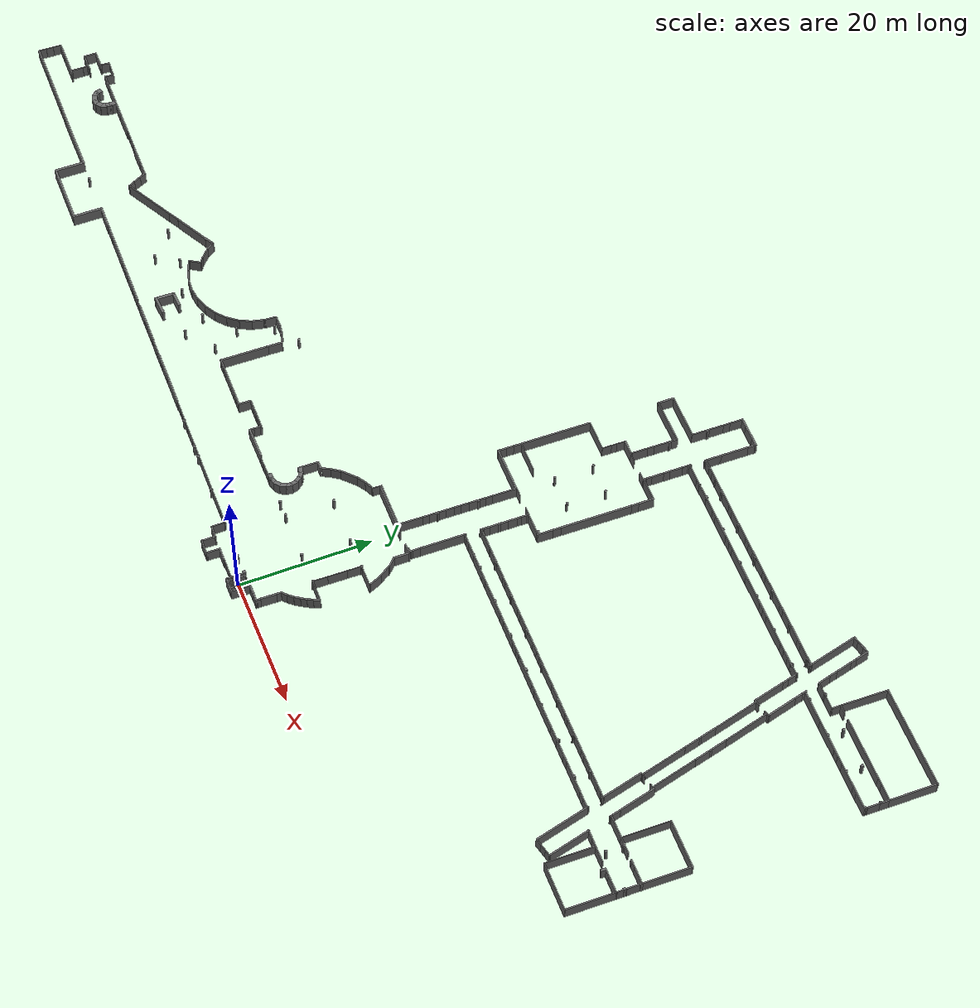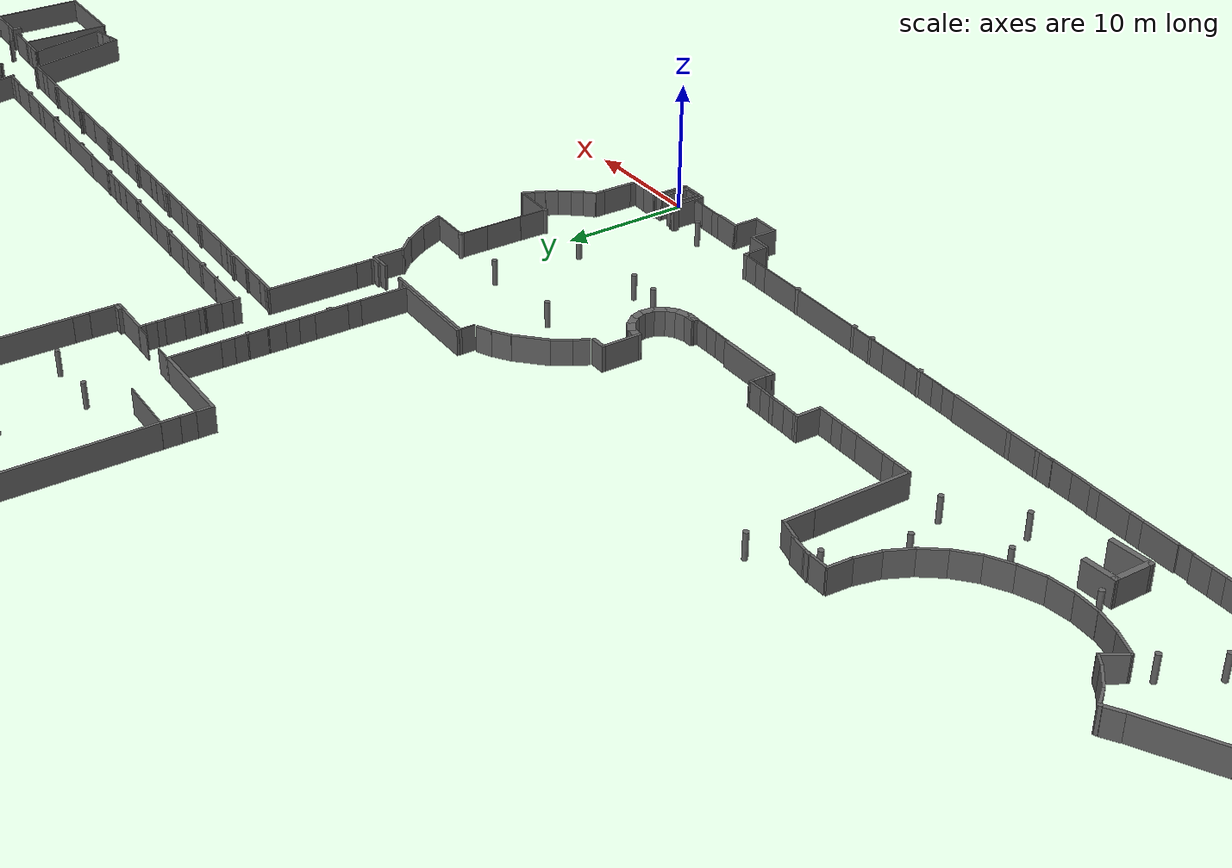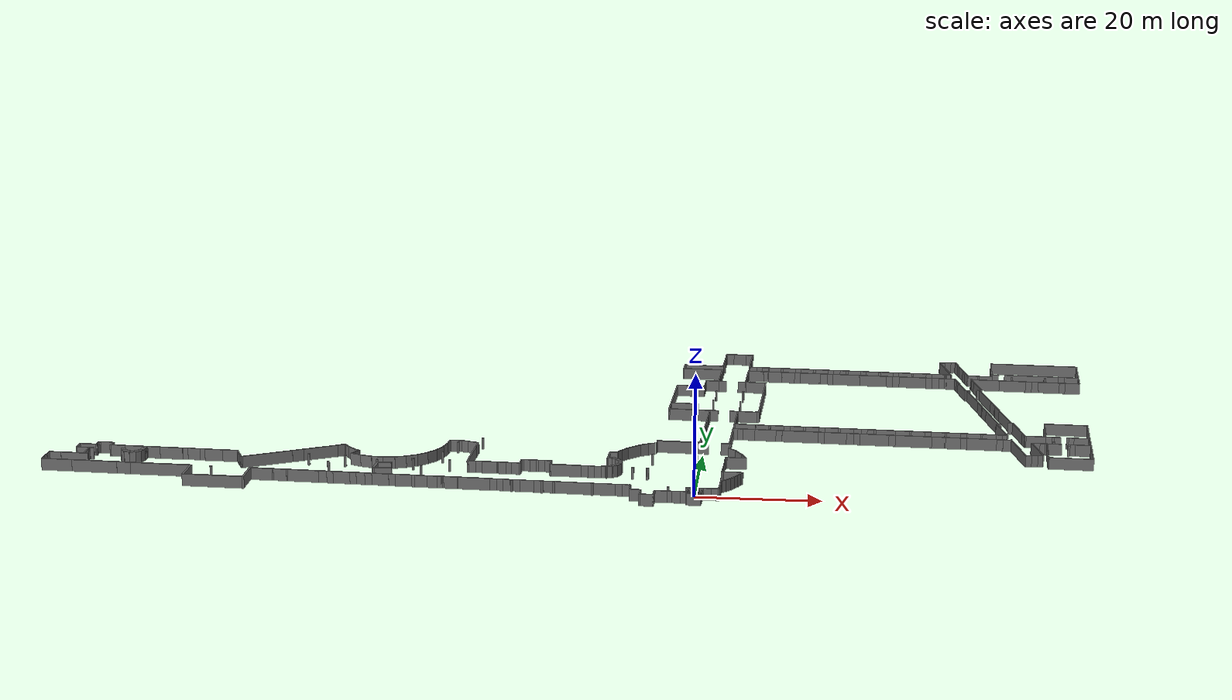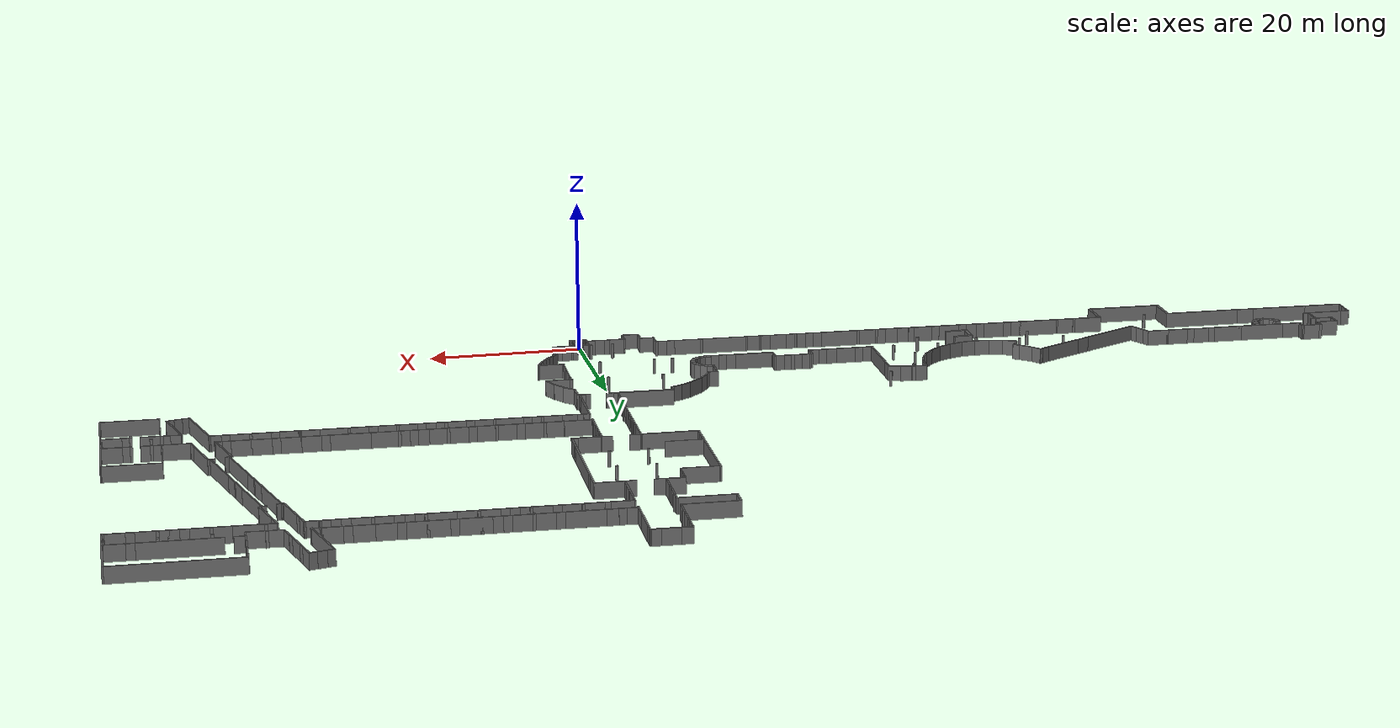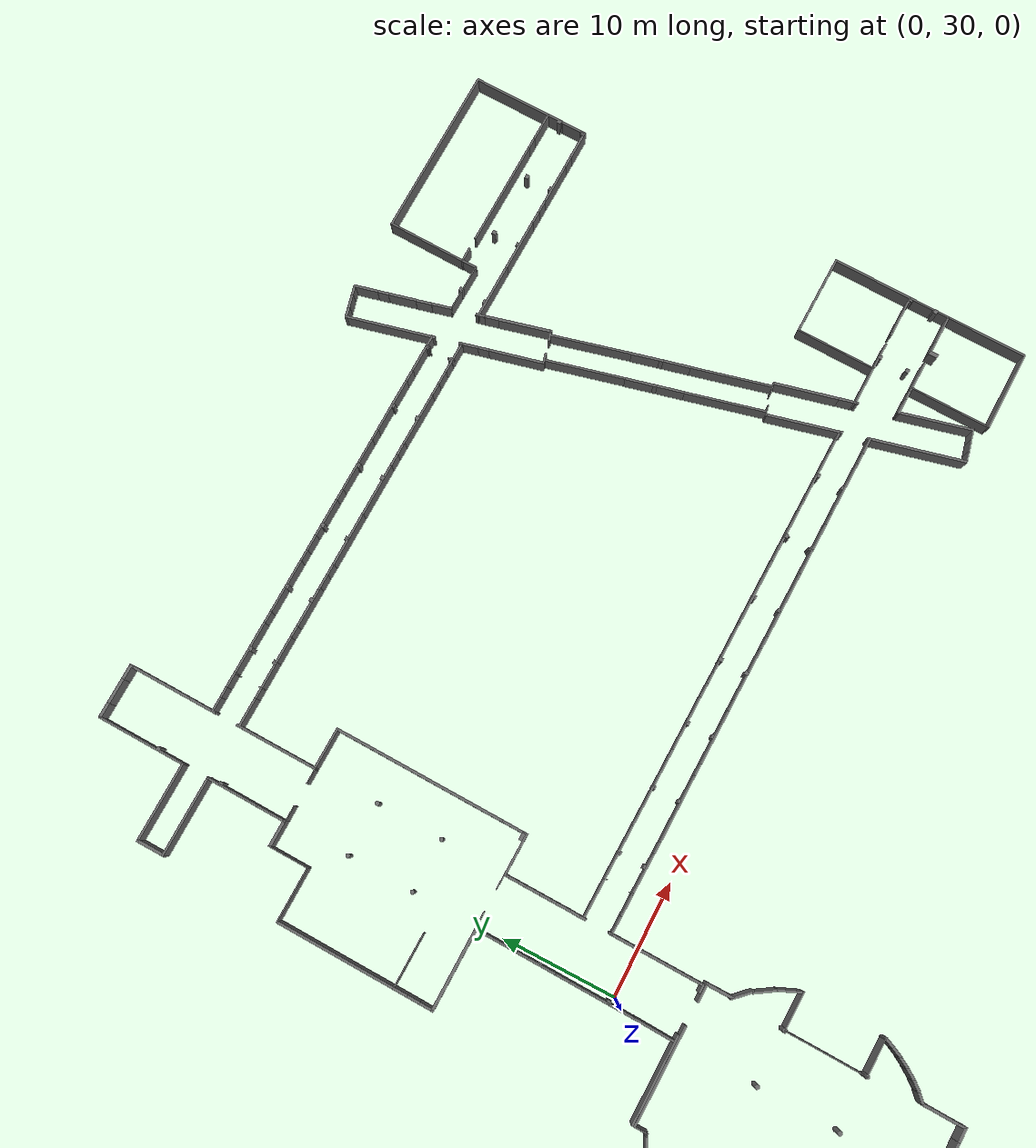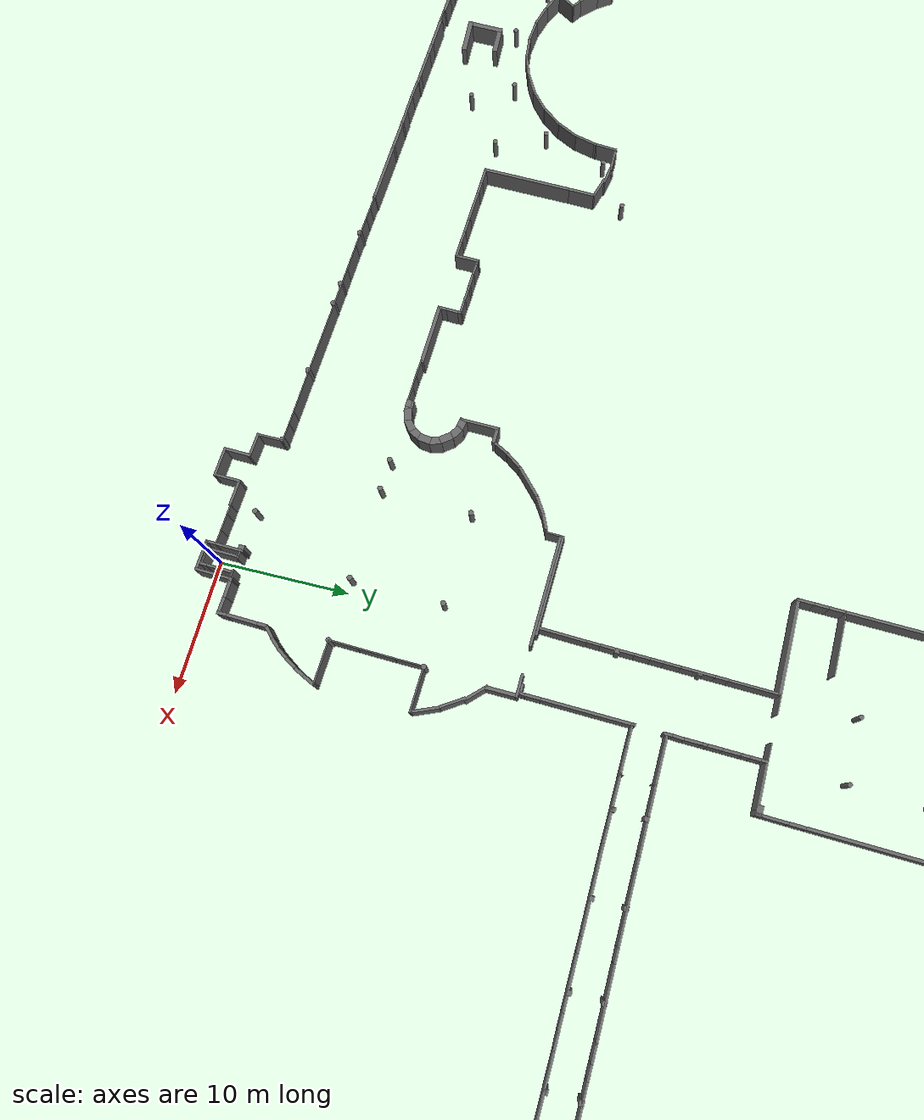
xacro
<?xml version="1.0"?>

<robot xmlns:xacro="http://www.ros.org/wiki/xacro" name="brsu-ground-floor">

    <xacro:include filename="$(find mcr_gazebo_worlds)/common/worlds/atwork_macros.xacro" />

    <!-- overwrite default height -->
    <xacro:property name="default_height" value="2.0" />

    <!-- ============================= MACROS ============================= -->

    <xacro:macro name="pillar" params="name parent *origin radius height:=${default_height}">
        <joint name="joint_${name}" type="fixed">
            <xacro:insert_block name="origin" />
            <parent link="${parent}"/>
            <child link="${name}"/>
        </joint>
        <link name="${name}">
            <visual>
                <origin xyz="0 0 0"/>
                <geometry>
                    <cylinder radius="${radius}" length="${height}" />
                </geometry>
                <material name="grey"/>
            </visual>
            <collision>
                <origin xyz="0 0 0"/>
                <geometry>
                    <cylinder radius="${radius}" length="${height}" />
                </geometry>
            </collision>
            <xacro:cuboid_inertia length="${radius*2}" width="${radius*2}" height="${height}" />
        </link>
        <gazebo reference="${name}">
            <material>Gazebo/White</material>
            <selfCollide>false</selfCollide>
        </gazebo>
    </xacro:macro>

    <!-- =========================== ACTUAL MAP =========================== -->
    <link name="origin"/>

    <xacro:wall name="wall_1" parent="origin" length="1.4737950172559886" width="0.08897760247026462">
        <origin xyz="3.8985647528024856 42.2313451487571 0.0" rpy="0.0 0.0 -0.03212817227871072"/>
    </xacro:wall>

    <xacro:wall name="wall_2" parent="origin" length="1.554844741247009" width="0.10022383415517466">
        <origin xyz="0.3968152056913823 42.31744179059751 0.0" rpy="0.0 0.0 3.1170105222626474"/>
    </xacro:wall>

    <xacro:wall name="wall_3" parent="origin" length="0.48940221235243897" width="0.21506923310879028">
        <origin xyz="4.526183830021182 42.010091348551214 0.0" rpy="0.0 0.0 -1.5809696010236158"/>
    </xacro:wall>

    <xacro:wall name="wall_4" parent="origin" length="3.8594099933194297" width="0.1833377710245494">
        <origin xyz="-0.33493256344809197 40.45521338726394 0.0" rpy="0.0 0.0 1.5480411681847481"/>
    </xacro:wall>

    <xacro:wall name="wall_5" parent="origin" length="0.7229602111043938" width="0.21506929026909455">
        <origin xyz="4.502449751496897 40.61441692826338 0.0" rpy="0.0 0.0 -1.5953776378629791"/>
    </xacro:wall>

    <xacro:wall name="wall_6" parent="origin" length="1.4125634340513809" width="0.22212078296460533">
        <origin xyz="4.480033334242762 39.7026720342692 0.0" rpy="0.0 0.0 1.5512070886322495"/>
    </xacro:wall>

    <xacro:wall name="wall_7" parent="origin" length="0.5227909670799815" width="0.22564659737710008">
        <origin xyz="4.434473342291312 37.63443777663633 0.0" rpy="0.0 0.0 -1.6088661339924415"/>
    </xacro:wall>

    <xacro:wall name="wall_8" parent="origin" length="1.3291401785908277" width="0.22577945732835306">
        <origin xyz="4.419067076873034 36.86437143757939 0.0" rpy="0.0 0.0 1.55678127721307"/>
    </xacro:wall>

    <xacro:wall name="wall_9" parent="origin" length="0.6284043106534635" width="0.21873663354325154">
        <origin xyz="4.364070330499089 35.05781989404932 0.0" rpy="0.0 0.0 -1.5953776202336285"/>
    </xacro:wall>

    <xacro:wall name="wall_10" parent="origin" length="2.535871488441578" width="0.19071440866537065">
        <origin xyz="-0.441248557282961 36.27461618115194 0.0" rpy="0.0 0.0 -1.5981470990192914"/>
    </xacro:wall>

    <xacro:wall name="wall_11" parent="origin" length="1.345786241517596" width="0.1903894407657193">
        <origin xyz="-0.4898811039456632 34.44009423744865 0.0" rpy="0.0 0.0 1.5462140684299064"/>
    </xacro:wall>

    <xacro:wall name="wall_12" parent="origin" length="1.75590523782869" width="0.20624379718532107">
        <origin xyz="3.599569305719342 24.04562228778377 0.0" rpy="0.0 0.0 -0.018246974409857467"/>
    </xacro:wall>

    <xacro:wall name="wall_13" parent="origin" length="8.67331752350453" width="0.20588158408796683">
        <origin xyz="-3.6190958933293587 24.217546700965613 0.0" rpy="0.0 0.0 -0.02458275932099035"/>
    </xacro:wall>

    <xacro:wall name="wall_14" parent="origin" length="7.777780344304057" width="0.1842085056681062">
        <origin xyz="-4.054758929647505 24.428518436150625 0.0" rpy="0.0 0.0 -0.024582845719723915"/>
    </xacro:wall>

    <xacro:wall name="wall_15" parent="origin" length="0.4115516041498937" width="0.21506996202485223">
        <origin xyz="4.123656488271081 24.347033963073045 0.0" rpy="0.0 0.0 1.5290815731084328"/>
    </xacro:wall>

    <xacro:wall name="wall_16" parent="origin" length="0.8109576808844943" width="0.18351630090136017">
        <origin xyz="3.8231563428853406 24.245947930961847 0.0" rpy="0.0 0.0 -0.024581334109016667"/>
    </xacro:wall>

    <xacro:wall name="wall_17" parent="origin" length="1.3235418341776144" width="0.1903895268579349">
        <origin xyz="-0.5478378806292312 32.08290015975945 0.0" rpy="0.0 0.0 1.5462140758104685"/>
    </xacro:wall>

    <xacro:wall name="wall_18" parent="origin" length="2.5247493088858466" width="0.19744106077822784">
        <origin xyz="-0.5921255924622528 30.281648087780923 0.0" rpy="0.0 0.0 1.543421139948591"/>
    </xacro:wall>

    <xacro:wall name="wall_19" parent="origin" length="6.823477031585034" width="0.21873247294301168">
        <origin xyz="4.225823180968291 29.1479830944445 0.0" rpy="0.0 0.0 -1.5933124588073049"/>
    </xacro:wall>

    <xacro:wall name="wall_20" parent="origin" length="3.7594789154059276" width="0.19391548685386892">
        <origin xyz="-0.710094358495553 26.12915135966614 0.0" rpy="0.0 0.0 1.5330846736132677"/>
    </xacro:wall>

    <xacro:wall name="wall_21" parent="origin" length="0.7675613483903558" width="0.23296531032088202">
        <origin xyz="3.8029414149496006 1.6198354645166546 0.0" rpy="0.0 0.0 -1.577002685914868"/>
    </xacro:wall>

    <xacro:wall name="wall_22" parent="origin" length="0.745204059312629" width="0.25032827425954296">
        <origin xyz="3.8849084699177183 4.738539989804849 0.0" rpy="0.0 0.0 -1.5953774706533739"/>
    </xacro:wall>

    <xacro:wall name="wall_23" parent="origin" length="2.2244511338862267" width="0.10577238602979186">
        <origin xyz="3.793957582282019 10.865397334331647 0.0" rpy="0.0 0.0 1.5430450857057674"/>
    </xacro:wall>

    <xacro:wall name="wall_24" parent="origin" length="3.4588292424083735" width="0.1113336516497705">
        <origin xyz="5.443700272386195 9.75678317528218 0.0" rpy="0.0 0.0 3.110587056818334"/>
    </xacro:wall>

    <xacro:wall name="wall_25" parent="origin" length="2.2356622601218863" width="0.09166931160795377">
        <origin xyz="3.9192977069324115 15.963385369395837 0.0" rpy="0.0 0.0 -1.5859151665820224"/>
    </xacro:wall>

    <xacro:wall name="wall_26" parent="origin" length="3.4693391090738994" width="0.12033762808952789">
        <origin xyz="5.623219089538907 16.98676542704925 0.0" rpy="0.0 0.0 3.11701172476077"/>
    </xacro:wall>

    <xacro:wall name="wall_27" parent="origin" length="1.3116232589031953" width="0.27805501265825583">
        <origin xyz="-14.565104589913972 17.5248729318846 0.0" rpy="0.0 0.0 3.1254876722953586"/>
    </xacro:wall>

    <xacro:wall name="wall_28" parent="origin" length="1.4856221934988518" width="0.21255113926738484">
        <origin xyz="-12.87592116939777 19.383026354713365 0.0" rpy="0.0 0.0 -2.1847085562003588"/>
    </xacro:wall>

    <xacro:wall name="wall_29" parent="origin" length="1.4507868075021149" width="0.23017173101860722">
        <origin xyz="-9.887553053136799 22.227223596768454 0.0" rpy="0.0 0.0 -2.565338059337987"/>
    </xacro:wall>

    <xacro:wall name="wall_30" parent="origin" length="2.4469855972009693" width="0.2679560962408714">
        <origin xyz="4.322919154350529 22.91250025574118 0.0" rpy="0.0 0.0 -1.5838507636022472"/>
    </xacro:wall>

    <xacro:wall name="wall_31" parent="origin" length="1.2790530469104517" width="0.11987508494888005">
        <origin xyz="-7.904189844994107 23.786098945885897 0.0" rpy="0.0 0.0 1.546212760692535"/>
    </xacro:wall>

    <xacro:wall name="wall_32" parent="origin" length="15.685856957876677" width="0.17801725679747926">
        <origin xyz="57.123668782485765 76.40797310159542 0.0" rpy="0.0 0.0 -0.0231530886873875"/>
    </xacro:wall>

    <xacro:wall name="wall_33" parent="origin" length="7.257234678333666" width="0.1905502445631152">
        <origin xyz="64.77898162942438 72.69581214641221 0.0" rpy="0.0 0.0 1.5462263162793841"/>
    </xacro:wall>

    <xacro:wall name="wall_34" parent="origin" length="7.229518945357194" width="0.16923374417672601">
        <origin xyz="49.259656606649514 73.06331533333287 0.0" rpy="0.0 0.0 1.5403711198290944"/>
    </xacro:wall>

    <xacro:wall name="wall_35" parent="origin" length="7.36876819063961" width="0.183516273428395">
        <origin xyz="60.41193853144068 40.800471062073484 0.0" rpy="0.0 0.0 -0.024570615648301108"/>
    </xacro:wall>

    <xacro:wall name="wall_36" parent="origin" length="7.340667718559887" width="0.18333778255060382">
        <origin xyz="63.905077022413025 37.134977407054976 0.0" rpy="0.0 0.0 1.5433446254839884"/>
    </xacro:wall>

    <xacro:wall name="wall_37" parent="origin" length="7.329532143974796" width="0.12692616694092293">
        <origin xyz="56.700803284635185 37.31758920266293 0.0" rpy="0.0 0.0 1.5452629788925643"/>
    </xacro:wall>

    <xacro:wall name="wall_38" parent="origin" length="7.361754821602762" width="0.15571077211514944">
        <origin xyz="59.95821898287977 22.768750448012725 0.0" rpy="0.0 0.0 -0.02154894655547646"/>
    </xacro:wall>

    <xacro:wall name="wall_39" parent="origin" length="7.385141140322663" width="0.17276096870255472">
        <origin xyz="63.64069990131247 26.30518285371363 0.0" rpy="0.0 0.0 -1.5953661927105425"/>
    </xacro:wall>

    <xacro:wall name="wall_40" parent="origin" length="7.396265185221246" width="0.13397789953666586">
        <origin xyz="56.43762699888612 26.465513775590807 0.0" rpy="0.0 0.0 -1.596320960947519"/>
    </xacro:wall>

    <xacro:wall name="wall_41" parent="origin" length="0.3460290850604116" width="0.19834435592921884">
        <origin xyz="46.6811730729969 49.657325002830476 0.0" rpy="0.0 0.0 -1.32725267558803"/>
    </xacro:wall>

    <xacro:wall name="wall_42" parent="origin" length="7.216017689658761" width="0.1683213200262582">
        <origin xyz="48.12743038732151 43.64179155253805 0.0" rpy="0.0 0.0 1.8084297437501888"/>
    </xacro:wall>

    <xacro:wall name="wall_43" parent="origin" length="7.184688393786644" width="0.1716382716469989">
        <origin xyz="45.22367767363903 55.717637702822685 0.0" rpy="0.0 0.0 1.8101778793682999"/>
    </xacro:wall>

    <xacro:wall name="wall_44" parent="origin" length="7.22793308896171" width="0.17163825225612805">
        <origin xyz="47.45882788073504 56.257918691728264 0.0" rpy="0.0 0.0 1.8146217829645312"/>
    </xacro:wall>

    <xacro:wall name="wall_45" parent="origin" length="0.3460290787555115" width="0.1983443342476982">
        <origin xyz="48.93706364827813 50.18040861492045 0.0" rpy="0.0 0.0 -1.327252274808418"/>
    </xacro:wall>

    <xacro:wall name="wall_46" parent="origin" length="7.216917540739026" width="0.16496523299765828">
        <origin xyz="50.38156102443463 44.16491914074868 0.0" rpy="0.0 0.0 1.8084301441307655"/>
    </xacro:wall>

    <xacro:wall name="wall_47" parent="origin" length="4.928984653223819" width="0.17795517916267897">
        <origin xyz="45.8634479912871 31.45376028981991 0.0" rpy="0.0 0.0 -0.026829820892441285"/>
    </xacro:wall>

    <xacro:wall name="wall_48" parent="origin" length="2.5103329176714926" width="0.18351628098094558">
        <origin xyz="41.136665031299344 31.561594021506608 0.0" rpy="0.0 0.0 -0.02457423786591085"/>
    </xacro:wall>

    <xacro:wall name="wall_49" parent="origin" length="1.5682457783590402" width="0.17628655990923825">
        <origin xyz="63.74102156145091 30.602744842180982 0.0" rpy="0.0 0.0 1.5507228631834966"/>
    </xacro:wall>

    <xacro:wall name="wall_50" parent="origin" length="0.42826269159201935" width="0.16941754773708348">
        <origin xyz="63.806969135199324 33.429796813754365 0.0" rpy="0.0 0.0 -1.6116211607852033"/>
    </xacro:wall>

    <xacro:wall name="wall_51" parent="origin" length="2.6795657438854557" width="0.17239407066974072">
        <origin xyz="62.558855351497186 33.58841324271634 0.0" rpy="0.0 0.0 -0.028720887633641338"/>
    </xacro:wall>

    <xacro:wall name="wall_52" parent="origin" length="0.3526606168638421" width="0.17239407126021355">
        <origin xyz="60.16208312670642 33.647314524045214 0.0" rpy="0.0 0.0 -0.02457060697643767"/>
    </xacro:wall>

    <xacro:wall name="wall_53" parent="origin" length="2.542062983710509" width="0.16135166628145947">
        <origin xyz="57.81994322137325 33.7048745858483 0.0" rpy="0.0 0.0 -0.020189722126750357"/>
    </xacro:wall>

    <xacro:wall name="wall_54" parent="origin" length="3.635026905378155" width="0.17040739446914127">
        <origin xyz="54.85576826972829 33.78050455148332 0.0" rpy="0.0 0.0 -0.024571627917342208"/>
    </xacro:wall>

    <xacro:wall name="wall_55" parent="origin" length="2.6654763600606937" width="0.1779551689016957">
        <origin xyz="62.48312423747848 29.932747756363824 0.0" rpy="0.0 0.0 -0.020397434568422905"/>
    </xacro:wall>

    <xacro:wall name="wall_56" parent="origin" length="2.5526418960438226" width="0.17239407313861113">
        <origin xyz="57.738853468734305 30.046559339622036 0.0" rpy="0.0 0.0 -0.020213917842809723"/>
    </xacro:wall>

    <xacro:wall name="wall_57" parent="origin" length="0.3879899412882837" width="0.17809482489757844">
        <origin xyz="56.399548138768296 30.082255501532927 0.0" rpy="0.0 0.0 -0.05324142861495023"/>
    </xacro:wall>

    <xacro:wall name="wall_58" parent="origin" length="1.0150325095668664" width="0.13028692674434253">
        <origin xyz="55.132917766764876 23.819100994383916 0.0" rpy="0.0 0.0 -2.9232011289107214"/>
    </xacro:wall>

    <xacro:wall name="wall_59" parent="origin" length="6.589426349562398" width="0.19803962259371827">
        <origin xyz="54.77835655493254 27.04310080735013 0.0" rpy="0.0 0.0 -1.3355422471290843"/>
    </xacro:wall>

    <xacro:wall name="wall_60" parent="origin" length="0.9590072468358288" width="0.07864823118324672">
        <origin xyz="49.063785984835704 40.19766892772168 0.0" rpy="0.0 0.0 0.23249294558027137"/>
    </xacro:wall>

    <xacro:wall name="wall_61" parent="origin" length="0.35502962472762334" width="0.2118360407315063">
        <origin xyz="50.78240754343278 31.41630415362306 0.0" rpy="0.0 0.0 -1.3470050783052077"/>
    </xacro:wall>

    <xacro:wall name="wall_62" parent="origin" length="0.8708899579612188" width="0.18524580079938904">
        <origin xyz="49.85406370280543 33.89508723700419 0.0" rpy="0.0 0.0 -0.012055060393962634"/>
    </xacro:wall>

    <xacro:wall name="wall_63" parent="origin" length="0.42231166615568644" width="0.2036770770769793">
        <origin xyz="53.15883312554797 33.758237407775596 0.0" rpy="0.0 0.0 -1.3107006117535511"/>
    </xacro:wall>

    <xacro:wall name="wall_64" parent="origin" length="6.52396690913983" width="0.2000051483499808">
        <origin xyz="49.44477830461983 36.973018983379006 0.0" rpy="0.0 0.0 1.805444409343841"/>
    </xacro:wall>

    <xacro:wall name="wall_65" parent="origin" length="8.444037895950956" width="0.2084797421258776">
        <origin xyz="51.76080328300304 27.314741370035335 0.0" rpy="0.0 0.0 1.8044908752161413"/>
    </xacro:wall>

    <xacro:wall name="wall_66" parent="origin" length="0.3560240473434319" width="0.2080180348335101">
        <origin xyz="50.20454897302261 33.805812877835706 0.0" rpy="0.0 0.0 1.8250851775589347"/>
    </xacro:wall>

    <xacro:wall name="wall_67" parent="origin" length="5.744091483390807" width="0.210597259689628">
        <origin xyz="52.15064395027002 38.01072743837722 0.0" rpy="0.0 0.0 -1.3386833349729954"/>
    </xacro:wall>

    <xacro:wall name="wall_68" parent="origin" length="0.9828901141978225" width="0.09145773859130757">
        <origin xyz="51.122831934073474 40.67552662710659 0.0" rpy="0.0 0.0 0.22702134553551143"/>
    </xacro:wall>

    <xacro:wall name="wall_69" parent="origin" length="1.0123477559586143" width="0.13179910956256713">
        <origin xyz="53.121722040785244 23.351191022899002 0.0" rpy="0.0 0.0 -2.93384338688065"/>
    </xacro:wall>

    <xacro:wall name="wall_70" parent="origin" length="1.523278282025467" width="0.18043533446920695">
        <origin xyz="50.145781363593414 31.342946363147348 0.0" rpy="0.0 0.0 3.131423621584188"/>
    </xacro:wall>

    <xacro:wall name="wall_71" parent="origin" length="1.4420461103224183" width="0.18687567537564528">
        <origin xyz="54.64989231726213 30.13916276092641 0.0" rpy="0.0 0.0 3.1091739703392287"/>
    </xacro:wall>

    <xacro:wall name="wall_72" parent="origin" length="2.538525155994483" width="0.16683297854340695">
        <origin xyz="47.11384165266645 33.970780157484114 0.0" rpy="0.0 0.0 -0.02457311059024433"/>
    </xacro:wall>

    <xacro:wall name="wall_73" parent="origin" length="2.524422257479935" width="0.16683298042270642">
        <origin xyz="44.724118819256546 34.02951545082033 0.0" rpy="0.0 0.0 -0.024573568942614202"/>
    </xacro:wall>

    <xacro:wall name="wall_74" parent="origin" length="2.4856891010729707" width="0.17802090209181404">
        <origin xyz="41.19050557988521 34.11080483882688 0.0" rpy="0.0 0.0 -0.02457424787427465"/>
    </xacro:wall>

    <xacro:wall name="wall_75" parent="origin" length="4.823232508594723" width="0.17239408976775072">
        <origin xyz="28.046053240119363 31.883367457659915 0.0" rpy="0.0 0.0 3.112403978992329"/>
    </xacro:wall>

    <xacro:wall name="wall_76" parent="origin" length="1.332749663332528" width="0.18351629125512608">
        <origin xyz="23.904433354036883 31.97961386386305 0.0" rpy="0.0 0.0 -0.024577543245052423"/>
    </xacro:wall>

    <xacro:wall name="wall_77" parent="origin" length="0.8743814318639391" width="0.1779552021248982">
        <origin xyz="4.6352866069209995 32.46167734824121 0.0" rpy="0.0 0.0 -0.024581241700099152"/>
    </xacro:wall>

    <xacro:wall name="wall_78" parent="origin" length="2.460971976737727" width="0.18365184693146516">
        <origin xyz="9.145810214089579 34.890192076796666 0.0" rpy="0.0 0.0 -0.029099821841699947"/>
    </xacro:wall>

    <xacro:wall name="wall_79" parent="origin" length="2.4821135563162584" width="0.18907738202548657">
        <origin xyz="38.781260461808415 34.164459923049435 0.0" rpy="0.0 0.0 -0.0245747095250114"/>
    </xacro:wall>

    <xacro:wall name="wall_80" parent="origin" length="4.907815514029947" width="0.1890773843878662">
        <origin xyz="34.04411083836749 34.28090002457611 0.0" rpy="0.0 0.0 -0.024575618394240707"/>
    </xacro:wall>

    <xacro:wall name="wall_81" parent="origin" length="2.055516519282409" width="0.18358612681990644">
        <origin xyz="6.927877109628753 32.39696768904105 0.0" rpy="0.0 0.0 3.1170118523233934"/>
    </xacro:wall>

    <xacro:wall name="wall_82" parent="origin" length="1.3398234259566495" width="0.17795519150624245">
        <origin xyz="25.154906049603596 34.499408774543554 0.0" rpy="0.0 0.0 -0.032878661766163886"/>
    </xacro:wall>

    <xacro:wall name="wall_83" parent="origin" length="4.907822001440536" width="0.1723940938296767">
        <origin xyz="22.165921942563727 34.57010480458848 0.0" rpy="0.0 0.0 -0.022311679991819846"/>
    </xacro:wall>

    <xacro:wall name="wall_84" parent="origin" length="3.751419567523512" width="0.18351629891971127">
        <origin xyz="9.633058631094173 32.330459700431675 0.0" rpy="0.0 0.0 3.111082779737849"/>
    </xacro:wall>

    <xacro:wall name="wall_85" parent="origin" length="4.893744269225238" width="0.16127188885225835">
        <origin xyz="29.278695594490273 34.395257422933355 0.0" rpy="0.0 0.0 -0.020031058659571284"/>
    </xacro:wall>

    <xacro:wall name="wall_86" parent="origin" length="6.071375807140348" width="0.18351629529208252">
        <origin xyz="15.586083660047734 32.17854435206391 0.0" rpy="0.0 0.0 3.122509240677522"/>
    </xacro:wall>

    <xacro:wall name="wall_87" parent="origin" length="4.893712880686204" width="0.16683299446248928">
        <origin xyz="16.230181398816057 34.70768142212182 0.0" rpy="0.0 0.0 -0.024579036684590782"/>
    </xacro:wall>

    <xacro:wall name="wall_88" parent="origin" length="3.709077769352558" width="0.1835162924605032">
        <origin xyz="21.51118477010459 32.038446720689535 0.0" rpy="0.0 0.0 3.117014650198787"/>
    </xacro:wall>

    <xacro:wall name="wall_89" parent="origin" length="6.064262862771987" width="0.18351628444394497">
        <origin xyz="34.573462463362375 31.71179150347598 0.0" rpy="0.0 0.0 3.1188512126353"/>
    </xacro:wall>

    <xacro:wall name="wall_90" parent="origin" length="2.5314739892854843" width="0.1779551978668802">
        <origin xyz="11.475545279972721 34.83013386907987 0.0" rpy="0.0 0.0 -0.02457994957474961"/>
    </xacro:wall>

    <xacro:wall name="wall_91" parent="origin" length="3.7126018515909998" width="0.18358202222946185">
        <origin xyz="6.11636086681392 34.96467321063392 0.0" rpy="0.0 0.0 -0.024580977752138727"/>
    </xacro:wall>

    <xacro:wall name="wall_92" parent="origin" length="0.33374050221750684" width="0.056411677963702736">
        <origin xyz="7.9421910133823985 34.85024871164933 0.0" rpy="0.0 0.0 1.5250855511991144"/>
    </xacro:wall>

    <xacro:wall name="wall_93" parent="origin" length="0.489402151057599" width="0.08109181509578858">
        <origin xyz="39.926311819042894 31.749882710631937 0.0" rpy="0.0 0.0 -1.5809627211026334"/>
    </xacro:wall>

    <xacro:wall name="wall_94" parent="origin" length="0.49496268694278395" width="0.07447620005660023">
        <origin xyz="39.98117572751653 33.981989982072264 0.0" rpy="0.0 0.0 1.560309768216569"/>
    </xacro:wall>

    <xacro:wall name="wall_95" parent="origin" length="2.4680118414244294" width="0.17795518374813088">
        <origin xyz="38.7329107051919 31.62345828488469 0.0" rpy="0.0 0.0 3.1170179549840733"/>
    </xacro:wall>

    <xacro:wall name="wall_96" parent="origin" length="0.3281434357055233" width="0.046553254785594626">
        <origin xyz="7.860302597808186 32.45192221435718 0.0" rpy="0.0 0.0 -1.6172354965572169"/>
    </xacro:wall>

    <xacro:wall name="wall_97" parent="origin" length="0.3225823519937" width="0.07403983719471047">
        <origin xyz="8.77444110129727 69.34684110525995 0.0" rpy="0.0 0.0 1.5462155811631315"/>
    </xacro:wall>

    <xacro:wall name="wall_98" parent="origin" length="0.3337032681598361" width="0.052885622277498705">
        <origin xyz="8.70495715837751 66.95099090598524 0.0" rpy="0.0 0.0 -1.6165070664694676"/>
    </xacro:wall>

    <xacro:wall name="wall_99" parent="origin" length="0.5005238120675963" width="0.08109127795650663">
        <origin xyz="40.77068571471318 66.24617341090925 0.0" rpy="0.0 0.0 -1.5953708995363711"/>
    </xacro:wall>

    <xacro:wall name="wall_100" parent="origin" length="0.5005238135948574" width="0.0740398310361991">
        <origin xyz="40.82561819376133 68.48106049979106 0.0" rpy="0.0 0.0 1.5462217321709457"/>
    </xacro:wall>

    <xacro:wall name="wall_101" parent="origin" length="2.85230878927295" width="0.18358613647274008">
        <origin xyz="6.472012858532253 66.93079250282608 0.0" rpy="0.0 0.0 3.1170114923901453"/>
    </xacro:wall>

    <xacro:wall name="wall_102" parent="origin" length="0.976652727230076" width="0.172463934904859">
        <origin xyz="8.265919519995805 66.88112466689199 0.0" rpy="0.0 0.0 3.117011837489624"/>
    </xacro:wall>

    <xacro:wall name="wall_103" parent="origin" length="2.531519565781109" width="0.17239410850114179">
        <origin xyz="9.899728289965424 66.84651939035393 0.0" rpy="0.0 0.0 3.1214057167329705"/>
    </xacro:wall>

    <xacro:wall name="wall_104" parent="origin" length="2.5244192938895464" width="0.18351630766416846">
        <origin xyz="12.265037192584714 66.79949329351075 0.0" rpy="0.0 0.0 3.117012604588448"/>
    </xacro:wall>

    <xacro:wall name="wall_105" parent="origin" length="3.7019935263574473" width="0.1890774059316835">
        <origin xyz="16.42038645397406 66.68899169075303 0.0" rpy="0.0 0.0 3.11701340193494"/>
    </xacro:wall>

    <xacro:wall name="wall_106" parent="origin" length="1.4173564726786472" width="0.18351630396205776">
        <origin xyz="18.75376856593357 66.63440898410045 0.0" rpy="0.0 0.0 3.124860952949795"/>
    </xacro:wall>

    <xacro:wall name="wall_107" parent="origin" length="4.8936827706540456" width="0.18907740244136967">
        <origin xyz="22.944500986050116 66.52860586764291 0.0" rpy="0.0 0.0 3.1170146537874683"/>
    </xacro:wall>

    <xacro:wall name="wall_108" parent="origin" length="4.8901633151615" width="0.1835820198466709">
        <origin xyz="27.7186985481967 66.41402558400296 0.0" rpy="0.0 0.0 3.119291612941363"/>
    </xacro:wall>

    <xacro:wall name="wall_109" parent="origin" length="1.2551766678119312" width="0.18351629725656954">
        <origin xyz="31.87601524188358 66.31183140887879 0.0" rpy="0.0 0.0 3.125877372824441"/>
    </xacro:wall>

    <xacro:wall name="wall_110" parent="origin" length="4.95715780835425" width="0.17795519478882832">
        <origin xyz="34.76262974861311 66.23809482017532 0.0" rpy="0.0 0.0 3.114773255274078"/>
    </xacro:wall>

    <xacro:wall name="wall_111" parent="origin" length="1.2798802841734958" width="0.17802501738978999">
        <origin xyz="39.0045379249932 66.13382700574584 0.0" rpy="0.0 0.0 3.125731881884276"/>
    </xacro:wall>

    <xacro:wall name="wall_112" parent="origin" length="1.4244293965120303" width="0.17795519159117978">
        <origin xyz="40.23640075715957 66.10354813677259 0.0" rpy="0.0 0.0 3.109209713774653"/>
    </xacro:wall>

    <xacro:wall name="wall_113" parent="origin" length="1.97090207122747" width="0.18131454840846933">
        <origin xyz="41.57400288811186 66.07067058770917 0.0" rpy="0.0 0.0 3.1225916724309277"/>
    </xacro:wall>

    <xacro:wall name="wall_114" parent="origin" length="0.35964204917712295" width="0.2152142652749578">
        <origin xyz="42.4362705177773 66.14126242743805 0.0" rpy="0.0 0.0 -1.3547096565419237"/>
    </xacro:wall>

    <xacro:wall name="wall_115" parent="origin" length="1.5310515505900504" width="0.20696619886544776">
        <origin xyz="42.610258014072315 65.39991770684719 0.0" rpy="0.0 0.0 1.807776542082258"/>
    </xacro:wall>

    <xacro:wall name="wall_116" parent="origin" length="4.8889333619397295" width="0.20512206922149456">
        <origin xyz="43.579157878717524 61.34308816189878 0.0" rpy="0.0 0.0 1.804371216600568"/>
    </xacro:wall>

    <xacro:wall name="wall_117" parent="origin" length="0.9953328443217597" width="0.17938056426154023">
        <origin xyz="44.50903795205522 59.142404712270945 0.0" rpy="0.0 0.0 -2.9073058648541052"/>
    </xacro:wall>

    <xacro:wall name="wall_118" parent="origin" length="1.011776659030761" width="0.1837946811813051">
        <origin xyz="46.562189187912736 59.66768884425983 0.0" rpy="0.0 0.0 -2.875313714737461"/>
    </xacro:wall>

    <xacro:wall name="wall_119" parent="origin" length="4.699902198035662" width="0.22912346757173324">
        <origin xyz="46.39643307105871 61.963627856457606 0.0" rpy="0.0 0.0 -1.329233993632868"/>
    </xacro:wall>

    <xacro:wall name="wall_120" parent="origin" length="0.6373903389603672" width="0.2093244141766644">
        <origin xyz="45.46699764607183 65.76081758411601 0.0" rpy="0.0 0.0 -1.3316257152644677"/>
    </xacro:wall>

    <xacro:wall name="wall_121" parent="origin" length="0.376722922854271" width="0.2044910485399529">
        <origin xyz="45.39866485145467 66.06566857243888 0.0" rpy="0.0 0.0 1.7909711385543956"/>
    </xacro:wall>

    <xacro:wall name="wall_122" parent="origin" length="1.9407275659351173" width="0.19789159524796246">
        <origin xyz="44.64615682710428 69.2410414533224 0.0" rpy="0.0 0.0 -1.3345079632135122"/>
    </xacro:wall>

    <xacro:wall name="wall_123" parent="origin" length="2.4919937034127897" width="0.20380893837983377">
        <origin xyz="43.83762534359994 72.57633070345037 0.0" rpy="0.0 0.0 -1.3327866012366234"/>
    </xacro:wall>

    <xacro:wall name="wall_124" parent="origin" length="2.144174726419907" width="0.2105958364646478">
        <origin xyz="43.07692270789994 75.77693783584982 0.0" rpy="0.0 0.0 -1.3400134364792415"/>
    </xacro:wall>

    <xacro:wall name="wall_125" parent="origin" length="0.9740907844548539" width="0.20016595314229146">
        <origin xyz="42.47559453936992 76.63726048823446 0.0" rpy="0.0 0.0 0.22702107125239948"/>
    </xacro:wall>

    <xacro:wall name="wall_126" parent="origin" length="0.9638539913758432" width="0.22410349265801405">
        <origin xyz="40.42672559138737 76.14246823382564 0.0" rpy="0.0 0.0 0.2324927021735248"/>
    </xacro:wall>

    <xacro:wall name="wall_127" parent="origin" length="7.847946888229117" width="0.1964781348203267">
        <origin xyz="40.941737152126734 72.34433814650401 0.0" rpy="0.0 0.0 1.8053525420268173"/>
    </xacro:wall>

    <xacro:wall name="wall_128" parent="origin" length="0.3623499914874201" width="0.204653254805368">
        <origin xyz="41.85489597891865 68.53085895371623 0.0" rpy="0.0 0.0 1.8350940374653515"/>
    </xacro:wall>

    <xacro:wall name="wall_129" parent="origin" length="5.059390651974644" width="0.1922457291458417">
        <origin xyz="47.844343360717176 65.91655384469777 0.0" rpy="0.0 0.0 3.117019434474446"/>
    </xacro:wall>

    <xacro:wall name="wall_130" parent="origin" length="4.872528067333398" width="0.18907738482752143">
        <origin xyz="52.61847277927154 65.79921662784182 0.0" rpy="0.0 0.0 3.117020348259676"/>
    </xacro:wall>

    <xacro:wall name="wall_131" parent="origin" length="1.3045118402184914" width="0.17795518282039074">
        <origin xyz="56.79151390114566 65.69109310675412 0.0" rpy="0.0 0.0 -0.024571504517702077"/>
    </xacro:wall>

    <xacro:wall name="wall_132" parent="origin" length="3.7795586010323134" width="0.1779551817786295">
        <origin xyz="59.142451049832744 65.63331624679267 0.0" rpy="0.0 0.0 3.117021599889228"/>
    </xacro:wall>

    <xacro:wall name="wall_133" parent="origin" length="2.6478181038956485" width="0.194700548986097">
        <origin xyz="63.37385378044564 65.53210822772235 0.0" rpy="0.0 0.0 -0.024570242462969794"/>
    </xacro:wall>

    <xacro:wall name="wall_134" parent="origin" length="0.5005237737643196" width="0.19391391129435503">
        <origin xyz="64.60432343451248 65.66040836530738 0.0" rpy="0.0 0.0 -1.5953663151401603"/>
    </xacro:wall>

    <xacro:wall name="wall_135" parent="origin" length="1.5571078134093037" width="0.19038810186338506">
        <origin xyz="64.67480688689102 68.45675373473205 0.0" rpy="0.0 0.0 -1.5953663605507913"/>
    </xacro:wall>

    <xacro:wall name="wall_136" parent="origin" length="2.623124618183999" width="0.1668329817231286">
        <origin xyz="63.4758835756802 69.18156482791528 0.0" rpy="0.0 0.0 -0.024570250867028093"/>
    </xacro:wall>

    <xacro:wall name="wall_137" parent="origin" length="9.674535100882286" width="0.16683298598257207">
        <origin xyz="56.28561608248856 69.35827410849743 0.0" rpy="0.0 0.0 -0.02457163052723841"/>
    </xacro:wall>

    <xacro:wall name="wall_138" parent="origin" length="1.4032307030293851" width="0.1668329892475053">
        <origin xyz="49.76855504326522 69.51844304078259 0.0" rpy="0.0 0.0 -0.024572881235903333"/>
    </xacro:wall>

    <xacro:wall name="wall_139" parent="origin" length="4.463827915722102" width="0.1074212531194233">
        <origin xyz="46.994205407900154 68.27659722045064 0.0" rpy="0.0 0.0 -0.03457180656063539"/>
    </xacro:wall>

    <xacro:wall name="wall_140" parent="origin" length="1.2869064407153186" width="0.1852457928839907">
        <origin xyz="41.294765349055524 68.62806835351512 0.0" rpy="0.0 0.0 -0.016048751555855428"/>
    </xacro:wall>

    <xacro:wall name="wall_141" parent="origin" length="2.6231253683738798" width="0.1890773922555403">
        <origin xyz="39.69274743106507 68.66466404963285 0.0" rpy="0.0 0.0 -0.024574805692139535"/>
    </xacro:wall>

    <xacro:wall name="wall_142" parent="origin" length="2.503263740869316" width="0.18351629411901457">
        <origin xyz="36.08710744268319 68.75607241876423 0.0" rpy="0.0 0.0 -0.029018570433415547"/>
    </xacro:wall>

    <xacro:wall name="wall_143" parent="origin" length="2.5455841788871068" width="0.1779551953052339">
        <origin xyz="33.697332147930865 68.81203332659788 0.0" rpy="0.0 0.0 -0.02020672905828017"/>
    </xacro:wall>

    <xacro:wall name="wall_144" parent="origin" length="3.723145876464101" width="0.17795520143500215">
        <origin xyz="23.620245411380893 69.05418439023197 0.0" rpy="0.0 0.0 -0.02457789029327222"/>
    </xacro:wall>

    <xacro:wall name="wall_145" parent="origin" length="1.4314583825841605" width="0.17239410167597868">
        <origin xyz="21.2762904913252 69.10902431374416 0.0" rpy="0.0 0.0 -0.02457833933895053"/>
    </xacro:wall>

    <xacro:wall name="wall_146" parent="origin" length="4.928937361077191" width="0.1668329986030516">
        <origin xyz="28.95289134106133 68.91753300651908 0.0" rpy="0.0 0.0 -0.024576866753687504"/>
    </xacro:wall>

    <xacro:wall name="wall_147" parent="origin" length="4.900731894297815" width="0.16683300515742683">
        <origin xyz="17.074849536948022 69.2095303889364 0.0" rpy="0.0 0.0 -0.024579146002678524"/>
    </xacro:wall>

    <xacro:wall name="wall_148" parent="origin" length="4.921886219454066" width="0.17795520773052087">
        <origin xyz="11.128916114932508 69.3612719734665 0.0" rpy="0.0 0.0 -0.024580287689628593"/>
    </xacro:wall>

    <xacro:wall name="wall_149" parent="origin" length="1.3679967255029006" width="0.18351631041484057">
        <origin xyz="8.175334953106358 69.43666816386394 0.0" rpy="0.0 0.0 -0.024580853724006622"/>
    </xacro:wall>

    <xacro:wall name="wall_150" parent="origin" length="1.4384882615913543" width="0.16683301074853987">
        <origin xyz="5.8277187585918 69.486042563105 0.0" rpy="0.0 0.0 -0.02458130387007624"/>
    </xacro:wall>

    <xacro:wall name="wall_151" parent="origin" length="0.3671003590107958" width="0.21154207625605734">
        <origin xyz="5.401993630526704 77.27327730320394 0.0" rpy="0.0 0.0 -1.6145873136538995"/>
    </xacro:wall>

    <xacro:wall name="wall_152" parent="origin" length="2.5581111200698494" width="0.2573766483780545">
        <origin xyz="-6.640282239866792 68.51872196234763 0.0" rpy="0.0 0.0 -1.5926235473552082"/>
    </xacro:wall>

    <xacro:wall name="wall_153" parent="origin" length="7.203026322348794" width="0.18358203744346102">
        <origin xyz="-3.1941693873377517 67.24633530993015 0.0" rpy="0.0 0.0 3.11700963718708"/>
    </xacro:wall>

    <xacro:wall name="wall_154" parent="origin" length="7.199497331288605" width="0.18351631730482215">
        <origin xyz="-3.1444755835836986 69.62598382937722 0.0" rpy="0.0 0.0 3.1170096281606976"/>
    </xacro:wall>

    <xacro:wall name="wall_155" parent="origin" length="0.33366602199440343" width="0.2115423952468866">
        <origin xyz="5.212380866898457 69.41772969230078 0.0" rpy="0.0 0.0 -1.5953777285649724"/>
    </xacro:wall>

    <xacro:wall name="wall_156" parent="origin" length="2.4802557826766556" width="0.21506804983509634">
        <origin xyz="5.241099527294864 70.65752375475131 0.0" rpy="0.0 0.0 -1.595377732327756"/>
    </xacro:wall>

    <xacro:wall name="wall_157" parent="origin" length="4.337658318238232" width="0.21859362136317684">
        <origin xyz="5.318478430330288 73.87647146335803 0.0" rpy="0.0 0.0 -1.5953777425015248"/>
    </xacro:wall>

    <xacro:wall name="wall_158" parent="origin" length="1.3538692779356518" width="0.26693282108631866">
        <origin xyz="4.835757395339897 77.33726411731914 0.0" rpy="0.0 0.0 -0.024581557000883866"/>
    </xacro:wall>

    <xacro:wall name="wall_159" parent="origin" length="1.4244050297959012" width="0.2613717225219213">
        <origin xyz="1.1913520330854226 77.42964999191463 0.0" rpy="0.0 0.0 -0.02458225586785866"/>
    </xacro:wall>

    <xacro:wall name="wall_160" parent="origin" length="2.14658479696105" width="0.17628509641951193">
        <origin xyz="0.5443222783069359 76.50266722566448 0.0" rpy="0.0 0.0 1.54621393734898"/>
    </xacro:wall>

    <xacro:wall name="wall_161" parent="origin" length="0.35962191301001745" width="0.333666028131959">
        <origin xyz="0.5231926418782678 71.91389227332547 0.0" rpy="0.0 0.0 -0.024582340383233234"/>
    </xacro:wall>

    <xacro:wall name="wall_162" parent="origin" length="4.94938444709251" width="0.17628525126854305">
        <origin xyz="0.4281640663102735 71.92179155210033 0.0" rpy="0.0 0.0 1.5447892461903765"/>
    </xacro:wall>

    <xacro:wall name="wall_163" parent="origin" length="3.7370594854010424" width="0.1833368912049485">
        <origin xyz="0.27460126116056927 65.38929941062815 0.0" rpy="0.0 0.0 1.546213972379622"/>
    </xacro:wall>

    <xacro:wall name="wall_164" parent="origin" length="0.36154031024601274" width="0.21168387575908537">
        <origin xyz="5.150696344746393 67.05228300811723 0.0" rpy="0.0 0.0 -1.615187464852963"/>
    </xacro:wall>

    <xacro:wall name="wall_165" parent="origin" length="0.4448880281573922" width="0.2044910832253575">
        <origin xyz="5.145433935671463 66.83824532735161 0.0" rpy="0.0 0.0 1.5462148927615296"/>
    </xacro:wall>

    <xacro:wall name="wall_166" parent="origin" length="0.3337032559531624" width="0.21506962337101776">
        <origin xyz="4.304119222753798 32.54769841581583 0.0" rpy="0.0 0.0 -1.5953776123626169"/>
    </xacro:wall>

    <xacro:wall name="wall_167" parent="origin" length="1.935262916042425" width="0.21154258157675104">
        <origin xyz="5.092428986346931 64.82582184066996 0.0" rpy="0.0 0.0 1.5462148976908745"/>
    </xacro:wall>

    <xacro:wall name="wall_168" parent="origin" length="1.8351631024398993" width="0.2115426983060434">
        <origin xyz="5.028811674492317 61.95142824342474 0.0" rpy="0.0 0.0 -1.5953777455507625"/>
    </xacro:wall>

    <xacro:wall name="wall_169" parent="origin" length="0.42823337812629125" width="0.2152145838262283">
        <origin xyz="4.981298752347357 59.94721391284838 0.0" rpy="0.0 0.0 1.5624698204957381"/>
    </xacro:wall>

    <xacro:wall name="wall_170" parent="origin" length="2.647083782934334" width="0.17628561477477522">
        <origin xyz="0.16041550981753971 61.175518861273304 0.0" rpy="0.0 0.0 1.5462139842357854"/>
    </xacro:wall>

    <xacro:wall name="wall_171" parent="origin" length="1.4949023626240168" width="0.07785540342882905">
        <origin xyz="4.340794191331952 59.78773407195695 0.0" rpy="0.0 0.0 3.1170111403657077"/>
    </xacro:wall>

    <xacro:wall name="wall_172" parent="origin" length="3.8359838718588724" width="0.17239410761666007">
        <origin xyz="6.788061700732214 59.774848924484104 0.0" rpy="0.0 0.0 3.1141121723884613"/>
    </xacro:wall>

    <xacro:wall name="wall_173" parent="origin" length="1.5619106872008128" width="0.07245364250530963">
        <origin xyz="0.8212281723535853 59.86592478421517 0.0" rpy="0.0 0.0 -0.024582188167181"/>
    </xacro:wall>

    <xacro:wall name="wall_174" parent="origin" length="2.418664774630546" width="0.2558106183645391">
        <origin xyz="-0.9899477750295773 60.002242708113045 0.0" rpy="0.0 0.0 -0.02918104144441586"/>
    </xacro:wall>

    <xacro:wall name="wall_175" parent="origin" length="1.4570168394328205" width="0.09584267888464704">
        <origin xyz="-2.166082140422077 59.430380527861416 0.0" rpy="0.0 0.0 1.5462135597277946"/>
    </xacro:wall>

    <xacro:wall name="wall_176" parent="origin" length="1.4236417000908004" width="0.09166859172384043">
        <origin xyz="-2.2233419841650175 57.17329927091487 0.0" rpy="0.0 0.0 -1.595379069092645"/>
    </xacro:wall>

    <xacro:wall name="wall_177" parent="origin" length="4.96420748481456" width="0.1000998078004875">
        <origin xyz="-4.67514181266597 56.571613600244746 0.0" rpy="0.0 0.0 -0.024583216623475162"/>
    </xacro:wall>

    <xacro:wall name="wall_178" parent="origin" length="1.3179901768107576" width="0.21521059847361812">
        <origin xyz="-7.385613506485242 42.939910327782854 0.0" rpy="0.0 0.0 -1.6007075963606092"/>
    </xacro:wall>

    <xacro:wall name="wall_179" parent="origin" length="1.290175288080822" width="0.2188776070658024">
        <origin xyz="-7.324729171799845 45.34431615192443 0.0" rpy="0.0 0.0 -1.595379941893593"/>
    </xacro:wall>

    <xacro:wall name="wall_180" parent="origin" length="4.907818707547019" width="0.10009980633310156">
        <origin xyz="-4.96620523056481 45.88154206657782 0.0" rpy="0.0 0.0 -0.026849411410010716"/>
    </xacro:wall>

    <xacro:wall name="wall_181" parent="origin" length="10.78853598680448" width="0.21506887390347265">
        <origin xyz="-7.1803609148046235 51.287379536777735 0.0" rpy="0.0 0.0 -1.5947263565396288"/>
    </xacro:wall>

    <xacro:wall name="wall_182" parent="origin" length="2.402483254518634" width="0.23622282689385418">
        <origin xyz="8.573951661790488 58.61004068842158 0.0" rpy="0.0 0.0 1.549150768517262"/>
    </xacro:wall>

    <xacro:wall name="wall_183" parent="origin" length="10.78297781929979" width="0.2398741433087651">
        <origin xyz="8.382816653858754 50.90750729688443 0.0" rpy="0.0 0.0 1.5449070772064324"/>
    </xacro:wall>

    <xacro:wall name="wall_184" parent="origin" length="0.765122908206946" width="0.48384110686505655">
        <origin xyz="7.885447971144458 42.22510936087929 0.0" rpy="0.0 0.0 -0.03918422121861376"/>
    </xacro:wall>

    <xacro:wall name="wall_185" parent="origin" length="2.341244326989059" width="0.2187318739108752">
        <origin xyz="8.18848426284967 43.146643365500495 0.0" rpy="0.0 0.0 -1.6013863345793131"/>
    </xacro:wall>

    <xacro:wall name="wall_186" parent="origin" length="3.8465659841804394" width="0.1891431253120359">
        <origin xyz="6.3415495257359 42.11565398750827 0.0" rpy="0.0 0.0 3.1170116628486837"/>
    </xacro:wall>

    <xacro:wall name="wall_187" parent="origin" length="7.301810656347294" width="0.2558591980873888">
        <origin xyz="-3.8525869792938465 42.33292066026479 0.0" rpy="0.0 0.0 -0.02153798980267821"/>
    </xacro:wall>

    <xacro:wall name="wall_188" parent="origin" length="0.6102068235765156" width="0.4394694600332923">
        <origin xyz="-15.496638974305824 10.263317083008587 0.0" rpy="0.0 0.0 3.135346169796531"/>
    </xacro:wall>

    <xacro:wall name="wall_189" parent="origin" length="3.1921027065937766" width="0.2115445922019531">
        <origin xyz="-15.143858314317185 16.076092856004834 0.0" rpy="0.0 0.0 -1.590963155139209"/>
    </xacro:wall>

    <xacro:wall name="wall_190" parent="origin" length="2.157706800599983" width="0.21859680100190637">
        <origin xyz="-8.411597450613044 -1.4397618360817432 0.0" rpy="0.0 0.0 1.5462128292638284"/>
    </xacro:wall>

    <xacro:wall name="wall_191" parent="origin" length="2.3834107214872846" width="0.200199599541671">
        <origin xyz="-7.353576306180912 -2.4448260923381895 0.0" rpy="0.0 0.0 3.1170093882989667"/>
    </xacro:wall>

    <xacro:wall name="wall_192" parent="origin" length="2.1799511850777678" width="0.19744227010340745">
        <origin xyz="-6.236590623753727 -1.4821158242411911 0.0" rpy="0.0 0.0 -1.5953794050056926"/>
    </xacro:wall>

    <xacro:wall name="wall_193" parent="origin" length="2.1084009800253742" width="0.21132179810194698">
        <origin xyz="-5.257204912835732 -0.5215845899656415 0.0" rpy="0.0 0.0 3.117009774320346"/>
    </xacro:wall>

    <xacro:wall name="wall_194" parent="origin" length="0.9660886337198142" width="0.10566089886835786">
        <origin xyz="-3.9306233197712572 -0.5013558552600443 0.0" rpy="0.0 0.0 3.128522507516436"/>
    </xacro:wall>

    <xacro:wall name="wall_195" parent="origin" length="1.1917308250491008" width="0.09453869880305132">
        <origin xyz="-1.597142616432393 -0.553167178761214 0.0" rpy="0.0 0.0 3.107677731750275"/>
    </xacro:wall>

    <xacro:wall name="wall_196" parent="origin" length="0.8039100868648164" width="0.10566089789635144">
        <origin xyz="0.8586072862381116 1.355677819577977 0.0" rpy="0.0 0.0 -0.010746813008843026"/>
    </xacro:wall>

    <xacro:wall name="wall_197" parent="origin" length="0.796858926762616" width="0.1056608982506273">
        <origin xyz="-0.7452622249838896 1.3895491021685302 0.0" rpy="0.0 0.0 -0.024582029494834574"/>
    </xacro:wall>

    <xacro:wall name="wall_198" parent="origin" length="0.5147599013271573" width="0.45601019279402244">
        <origin xyz="-1.2109993916528765 1.3815304541494697 0.0" rpy="0.0 0.0 3.117010536528791"/>
    </xacro:wall>

    <xacro:wall name="wall_199" parent="origin" length="2.2244455448026095" width="0.19391643473060885">
        <origin xyz="-1.0723597650357988 0.493639602791518 0.0" rpy="0.0 0.0 1.543044219544981"/>
    </xacro:wall>

    <xacro:wall name="wall_200" parent="origin" length="0.8675602387075088" width="0.2044937507378467">
        <origin xyz="-1.1096614194539143 -0.9517661991994828 0.0" rpy="0.0 0.0 1.5543422918534726"/>
    </xacro:wall>

    <xacro:wall name="wall_201" parent="origin" length="2.404564591262151" width="0.21132179517731076">
        <origin xyz="-0.014498346281470731 -1.3068968050647527 0.0" rpy="0.0 0.0 3.117010786183794"/>
    </xacro:wall>

    <xacro:wall name="wall_202" parent="origin" length="2.9974535283610253" width="0.20111907244872074">
        <origin xyz="1.1282566162990406 0.05848297057673335 0.0" rpy="0.0 0.0 1.5415184030266347"/>
    </xacro:wall>

    <xacro:wall name="wall_203" parent="origin" length="0.2752335231313298" width="0.2670260786967272">
        <origin xyz="1.2058719421766 1.4222372698131949 0.0" rpy="0.0 0.0 3.0765899447360923"/>
    </xacro:wall>

    <xacro:wall name="wall_204" parent="origin" length="1.3221572341075278" width="0.2558591756663292">
        <origin xyz="3.255751083299401 1.3829636999871582 0.0" rpy="0.0 0.0 3.1170113922944895"/>
    </xacro:wall>

    <xacro:wall name="wall_205" parent="origin" length="1.4683758058975533" width="0.16570816788208234">
        <origin xyz="49.151616998104146 68.88276088424027 0.0" rpy="0.0 0.0 1.5558290275821713"/>
    </xacro:wall>

    <xacro:wall name="wall_206" parent="origin" length="0.38401163687901874" width="0.13071016332708063">
        <origin xyz="-100.83304506154673 10.198504923144355 0.0" rpy="0.0 0.0 1.5461950293616626"/>
    </xacro:wall>

    <xacro:wall name="wall_207" parent="origin" length="0.4671857615215391" width="0.12692701362583583">
        <origin xyz="-100.86130953718384 8.978169105248526 0.0" rpy="0.0 0.0 -1.580303452719868"/>
    </xacro:wall>

    <xacro:wall name="wall_208" parent="origin" length="1.8933456348907731" width="0.10578493682086676">
        <origin xyz="-23.41644715736038 2.00264234514907 0.0" rpy="0.0 0.0 -0.024586380375826306"/>
    </xacro:wall>

    <xacro:wall name="wall_209" parent="origin" length="1.3539119792084564" width="0.09453870507436554">
        <origin xyz="-24.976121311017778 2.04099700669758 0.0" rpy="0.0 0.0 -0.0163718627832609"/>
    </xacro:wall>

    <xacro:wall name="wall_210" parent="origin" length="2.002157445926837" width="0.1621846558834909">
        <origin xyz="-10.16781741619343 0.7172779033426195 0.0" rpy="0.0 0.0 -1.5777708018476193"/>
    </xacro:wall>

    <xacro:wall name="wall_211" parent="origin" length="1.4984655302827026" width="0.0835758423668545">
        <origin xyz="-10.819077718842891 1.6984341931529343 0.0" rpy="0.0 0.0 -0.031988898442958255"/>
    </xacro:wall>

    <xacro:wall name="wall_212" parent="origin" length="3.769046200737003" width="0.08967245989021988">
        <origin xyz="-14.513018479265156 1.7864844002760947 0.0" rpy="0.0 0.0 -0.02162543010270678"/>
    </xacro:wall>

    <xacro:wall name="wall_213" parent="origin" length="6.2123815940030545" width="0.09503300493824202">
        <origin xyz="-19.431788079047692 1.9046566218603402 0.0" rpy="0.0 0.0 -0.026377976739404053"/>
    </xacro:wall>

    <xacro:wall name="wall_214" parent="origin" length="1.255192957961007" width="0.12827684055381003">
        <origin xyz="-52.456360963435145 2.6445373380556703 0.0" rpy="0.0 0.0 3.1259116525187367"/>
    </xacro:wall>

    <xacro:wall name="wall_215" parent="origin" length="1.1847815928705456" width="0.10589658881131991">
        <origin xyz="-16.280910330679035 10.137969992822036 0.0" rpy="0.0 0.0 -0.0058101071087868165"/>
    </xacro:wall>

    <xacro:wall name="wall_216" parent="origin" length="1.329140577872572" width="0.10608483589840265">
        <origin xyz="-106.81559835147345 6.930166432633996 0.0" rpy="0.0 0.0 1.5461939106496925"/>
    </xacro:wall>

    <xacro:wall name="wall_217" parent="origin" length="1.2901852420823945" width="0.10929836064196033">
        <origin xyz="-106.89076339527674 4.520548664499074 0.0" rpy="0.0 0.0 1.5407284287059235"/>
    </xacro:wall>

    <xacro:wall name="wall_218" parent="origin" length="5.43673716876112" width="0.21711800378002147">
        <origin xyz="-102.92298664966074 7.462976363953203 0.0" rpy="0.0 0.0 3.1149425750066695"/>
    </xacro:wall>

    <xacro:wall name="wall_219" parent="origin" length="3.060370779041439" width="0.20019966064388153">
        <origin xyz="-101.65746278873121 10.305014208890498 0.0" rpy="0.0 0.0 -0.020967168976841484"/>
    </xacro:wall>

    <xacro:wall name="wall_220" parent="origin" length="2.079852051411239" width="0.2185964310236082">
        <origin xyz="-103.05492766978568 11.273948657792062 0.0" rpy="0.0 0.0 -1.595398067105165"/>
    </xacro:wall>

    <xacro:wall name="wall_221" parent="origin" length="2.8946393017875107" width="0.20026173484870982">
        <origin xyz="-101.69419209266198 12.180576513754204 0.0" rpy="0.0 0.0 3.116991187802131"/>
    </xacro:wall>

    <xacro:wall name="wall_222" parent="origin" length="0.35610057028137554" width="0.2002617341009424">
        <origin xyz="-100.26669614920684 12.145450931973755 0.0" rpy="0.0 0.0 3.1169914622482184"/>
    </xacro:wall>

    <xacro:wall name="wall_223" parent="origin" length="1.5414577733950172" width="0.19759838366302712">
        <origin xyz="-100.30484479606093 12.816705211997032 0.0" rpy="0.0 0.0 -1.6318706728394345"/>
    </xacro:wall>

    <xacro:wall name="wall_224" parent="origin" length="0.3526624199153723" width="0.08341652590808736">
        <origin xyz="-100.18118410385796 13.542387231253088 0.0" rpy="0.0 0.0 3.085456264745081"/>
    </xacro:wall>

    <xacro:wall name="wall_225" parent="origin" length="0.32798981216288925" width="0.08355601519856298">
        <origin xyz="-97.69982506663655 13.409014925127849 0.0" rpy="0.0 0.0 3.1169919440575153"/>
    </xacro:wall>

    <xacro:wall name="wall_226" parent="origin" length="1.463529373798541" width="0.17294418178953935">
        <origin xyz="-97.66025574346713 12.723818755475804 0.0" rpy="0.0 0.0 1.5123306465693431"/>
    </xacro:wall>

    <xacro:wall name="wall_227" parent="origin" length="0.3809432040282956" width="0.18960449799140194">
        <origin xyz="-97.79765685899474 12.084697952494025 0.0" rpy="0.0 0.0 -0.053801352763887304"/>
    </xacro:wall>

    <xacro:wall name="wall_228" parent="origin" length="2.6126266873007893" width="0.1894185068131302">
        <origin xyz="-96.47780047610286 12.046659529209137 0.0" rpy="0.0 0.0 -0.024600463878344584"/>
    </xacro:wall>

    <xacro:wall name="wall_229" parent="origin" length="6.353407879959338" width="0.21132185803905457">
        <origin xyz="-92.18311298868502 11.935426694341004 0.0" rpy="0.0 0.0 3.1187436024006487"/>
    </xacro:wall>

    <xacro:wall name="wall_230" parent="origin" length="3.85716840551636" width="0.2224440573499592">
        <origin xyz="-87.44594117160887 11.818872002186254 0.0" rpy="0.0 0.0 3.1169939223921177"/>
    </xacro:wall>

    <xacro:wall name="wall_231" parent="origin" length="1.092981885954622" width="0.10009982583656646">
        <origin xyz="-85.18864047800889 11.824524853844196 0.0" rpy="0.0 0.0 3.116994354818858"/>
    </xacro:wall>

    <xacro:wall name="wall_232" parent="origin" length="1.0121960807822874" width="0.12243730472608601">
        <origin xyz="-82.06469429118442 11.719852601876482 0.0" rpy="0.0 0.0 -0.03555061344153237"/>
    </xacro:wall>

    <xacro:wall name="wall_233" parent="origin" length="3.0110709696376015" width="0.22255579163587275">
        <origin xyz="-80.21709307449055 11.629894943209365 0.0" rpy="0.0 0.0 -0.017209737353714546"/>
    </xacro:wall>

    <xacro:wall name="wall_234" parent="origin" length="2.866454681648383" width="0.2113777169824727">
        <origin xyz="-77.51162648964964 11.574460476404056 0.0" rpy="0.0 0.0 3.1131109152862932"/>
    </xacro:wall>

    <xacro:wall name="wall_235" parent="origin" length="1.1016626558580498" width="0.21583295889450893">
        <origin xyz="-75.96133932386874 11.082953794160858 0.0" rpy="0.0 0.0 1.9638869019097138"/>
    </xacro:wall>

    <xacro:wall name="wall_236" parent="origin" length="1.127596181149554" width="0.20004327140429545">
        <origin xyz="-74.94274992746068 8.977413925807923 0.0" rpy="0.0 0.0 -1.0936874473890883"/>
    </xacro:wall>

    <xacro:wall name="wall_237" parent="origin" length="8.694378161137365" width="0.19264362564567308">
        <origin xyz="-70.96675518617849 10.53453040518798 0.0" rpy="0.0 0.0 -2.659080998090662"/>
    </xacro:wall>

    <xacro:wall name="wall_238" parent="origin" length="5.785900445744941" width="0.23029452429251318">
        <origin xyz="-62.974344858623226 14.718610188690946 0.0" rpy="0.0 0.0 -2.661096396421027"/>
    </xacro:wall>

    <xacro:wall name="wall_239" parent="origin" length="0.3028854779595681" width="0.28544456996502293">
        <origin xyz="-59.21251667787146 16.745494053000584 0.0" rpy="0.0 0.0 -2.7727520122941494"/>
    </xacro:wall>

    <xacro:wall name="wall_240" parent="origin" length="1.542821001817718" width="0.1879125656990655">
        <origin xyz="-58.80172620920348 16.240301629528403 0.0" rpy="0.0 0.0 2.1727053188889998"/>
    </xacro:wall>

    <xacro:wall name="wall_241" parent="origin" length="0.9618823952494209" width="0.17585659038026247">
        <origin xyz="-56.59830729238456 14.055555948754773 0.0" rpy="0.0 0.0 -0.5854338835032032"/>
    </xacro:wall>

    <xacro:wall name="wall_242" parent="origin" length="1.9684612749506702" width="0.2092983173381853">
        <origin xyz="-56.76315737910045 13.088905259501189 0.0" rpy="0.0 0.0 1.0082085746836968"/>
    </xacro:wall>

    <xacro:wall name="wall_243" parent="origin" length="2.469179044455302" width="0.23975045128030736">
        <origin xyz="-37.4728905683296 18.91151200304739 0.0" rpy="0.0 0.0 1.537639728416337"/>
    </xacro:wall>

    <xacro:wall name="wall_244" parent="origin" length="7.418530032160915" width="0.2503278990336985">
        <origin xyz="-37.590462544874754 14.202727005118504 0.0" rpy="0.0 0.0 1.5490586821045687"/>
    </xacro:wall>

    <xacro:wall name="wall_245" parent="origin" length="1.435000632878631" width="0.2171738280464356">
        <origin xyz="-37.07261272704636 10.593652286566794 0.0" rpy="0.0 0.0 3.1170035867167742"/>
    </xacro:wall>

    <xacro:wall name="wall_246" parent="origin" length="2.743054088119333" width="0.20019961816842713">
        <origin xyz="-33.96201275567 10.519932572729886 0.0" rpy="0.0 0.0 -0.02864315797360672"/>
    </xacro:wall>

    <xacro:wall name="wall_247" parent="origin" length="1.5090609002862998" width="0.20019961738502604">
        <origin xyz="-32.14680167408369 10.475290505215526 0.0" rpy="0.0 0.0 3.1243748789893906"/>
    </xacro:wall>

    <xacro:wall name="wall_248" parent="origin" length="1.4526292341191627" width="0.19463851629212092">
        <origin xyz="-29.68677890628169 10.406447381479666 0.0" rpy="0.0 0.0 3.1170050057425436"/>
    </xacro:wall>

    <xacro:wall name="wall_249" parent="origin" length="2.0298077758545" width="0.22930636814980856">
        <origin xyz="-29.052824549828074 11.303153007058427 0.0" rpy="0.0 0.0 1.5462088151489228"/>
    </xacro:wall>

    <xacro:wall name="wall_250" parent="origin" length="0.43719252773167044" width="0.18907741500647046">
        <origin xyz="-28.922694639477413 12.220593190286309 0.0" rpy="0.0 0.0 3.1170051390559004"/>
    </xacro:wall>

    <xacro:wall name="wall_251" parent="origin" length="1.2588879304544052" width="0.18914313612619035">
        <origin xyz="-27.07427314769302 12.164010734995827 0.0" rpy="0.0 0.0 -0.006866733679460576"/>
    </xacro:wall>

    <xacro:wall name="wall_252" parent="origin" length="0.39848761745956657" width="0.1949632018290203">
        <origin xyz="-26.436100895734853 12.156660905806348 0.0" rpy="0.0 0.0 -0.02458703789111287"/>
    </xacro:wall>

    <xacro:wall name="wall_253" parent="origin" length="1.2729160414544973" width="0.17246393806504057">
        <origin xyz="-24.627939785568742 12.112194966292009 0.0" rpy="0.0 0.0 3.134529536280466"/>
    </xacro:wall>

    <xacro:wall name="wall_254" parent="origin" length="0.3284079641679656" width="0.21872908854768297">
        <origin xyz="-24.09911594101868 12.032436925685033 0.0" rpy="0.0 0.0 1.5025133045607961"/>
    </xacro:wall>

    <xacro:wall name="wall_255" parent="origin" length="0.7563425216990871" width="0.21154483077284808">
        <origin xyz="-24.142326343950117 10.562143792631105 0.0" rpy="0.0 0.0 1.536886435401777"/>
    </xacro:wall>

    <xacro:wall name="wall_256" parent="origin" length="5.144498134567295" width="0.28922019778424973">
        <origin xyz="-21.68173322273651 10.301375093171373 0.0" rpy="0.0 0.0 -0.01160509069274044"/>
    </xacro:wall>

    <xacro:wall name="wall_257" parent="origin" length="1.4209629986390944" width="0.11134603626161527">
        <origin xyz="-18.58490505431837 10.169593301601708 0.0" rpy="0.0 0.0 3.1013917444802424"/>
    </xacro:wall>

    <xacro:wall name="wall_258" parent="origin" length="2.669018209346882" width="0.10022383813968139">
        <origin xyz="-29.27129462697485 2.1327172839082778 0.0" rpy="0.0 0.0 -0.028760177790186907"/>
    </xacro:wall>

    <xacro:wall name="wall_259" parent="origin" length="1.33273464961255" width="0.1000998081350459">
        <origin xyz="-32.289779154598364 2.2236383338458836 0.0" rpy="0.0 0.0 3.1170045711633727"/>
    </xacro:wall>

    <xacro:wall name="wall_260" parent="origin" length="5.140547988444663" width="0.24468842126240975">
        <origin xyz="-35.321146951813716 2.2926275718491524 0.0" rpy="0.0 0.0 -0.024588664821009982"/>
    </xacro:wall>

    <xacro:wall name="wall_261" parent="origin" length="0.36684696488810475" width="0.24479000893837355">
        <origin xyz="-37.87993319747329 2.3611201709136367 0.0" rpy="0.0 0.0 0.005733860290486606"/>
    </xacro:wall>

    <xacro:wall name="wall_262" parent="origin" length="0.3809437934820864" width="0.2448914700749369">
        <origin xyz="-40.414456806582166 2.4123295820318162 0.0" rpy="0.0 0.0 0.004080322282226659"/>
    </xacro:wall>

    <xacro:wall name="wall_263" parent="origin" length="1.2939992045186814" width="0.24473921885690136">
        <origin xyz="-41.0365641079552 2.4276301353238523 0.0" rpy="0.0 0.0 -0.033161726359355465"/>
    </xacro:wall>

    <xacro:wall name="wall_264" parent="origin" length="0.7757454376981373" width="0.2335662283436332">
        <origin xyz="-45.292487230472034 2.5378678617998958 0.0" rpy="0.0 0.0 -0.010252649633387885"/>
    </xacro:wall>

    <xacro:wall name="wall_265" parent="origin" length="2.6443149073238" width="0.2335662286130235">
        <origin xyz="-46.80471479042899 2.5694994993973523 0.0" rpy="0.0 0.0 -0.024590868241027988"/>
    </xacro:wall>

    <xacro:wall name="wall_266" parent="origin" length="2.76420173854022" width="0.25024953441305225">
        <origin xyz="-50.55152567996993 2.658875378780067 0.0" rpy="0.0 0.0 -0.020567934971898346"/>
    </xacro:wall>

    <xacro:wall name="wall_267" parent="origin" length="1.4843629194079702" width="0.25030033026926185">
        <origin xyz="-53.73960525781149 2.7372919677291065 0.0" rpy="0.0 0.0 -0.017117076866898853"/>
    </xacro:wall>

    <xacro:wall name="wall_268" parent="origin" length="2.7642017879133247" width="0.2503489167407536">
        <origin xyz="-56.906263195109204 2.826309411553666 0.0" rpy="0.0 0.0 -0.02861645990992617"/>
    </xacro:wall>

    <xacro:wall name="wall_269" parent="origin" length="1.368014907929494" width="0.2502495423459484">
        <origin xyz="-60.011649339750875 2.897132975747809 0.0" rpy="0.0 0.0 -0.024593402968313444"/>
    </xacro:wall>

    <xacro:wall name="wall_270" parent="origin" length="5.288630081380122" width="0.2446884426929481">
        <origin xyz="-63.155601894221036 2.977252024691552 0.0" rpy="0.0 0.0 -0.024594005884691728"/>
    </xacro:wall>

    <xacro:wall name="wall_271" parent="origin" length="0.37389532387420166" width="0.23367266387103675">
        <origin xyz="-65.78501849986787 3.041932948632166 0.0" rpy="0.0 0.0 0.00515671021166682"/>
    </xacro:wall>

    <xacro:wall name="wall_272" parent="origin" length="0.3808625717137696" width="0.2395430855598895">
        <origin xyz="-68.32286160496005 3.1015817718580365 0.0" rpy="0.0 0.0 0.0046055924475685295"/>
    </xacro:wall>

    <xacro:wall name="wall_273" parent="origin" length="3.839690513080326" width="0.27826543436499823">
        <origin xyz="-70.23873418961011 3.140368683030829 0.0" rpy="0.0 0.0 -0.03326152398317912"/>
    </xacro:wall>

    <xacro:wall name="wall_274" parent="origin" length="10.295311873027414" width="0.2724939674515673">
        <origin xyz="-86.79304248921108 3.5226060203276575 0.0" rpy="0.0 0.0 -0.018116658768807033"/>
    </xacro:wall>

    <xacro:wall name="wall_275" parent="origin" length="7.587426268075662" width="0.25024957246149665">
        <origin xyz="-98.02296885359101 3.787786931497976 0.0" rpy="0.0 0.0 -0.024600696230353863"/>
    </xacro:wall>

    <xacro:wall name="wall_276" parent="origin" length="5.352117505729691" width="0.24468847562346785">
        <origin xyz="-104.28654278826434 3.9335651949513704 0.0" rpy="0.0 0.0 -0.020445715792419595"/>
    </xacro:wall>

    <xacro:wall name="wall_277" parent="origin" length="2.567528630180882" width="0.41263602477294226">
        <origin xyz="-51.03358552647114 8.152854791143909 0.0" rpy="0.0 0.0 0.04975375265068133"/>
    </xacro:wall>

    <xacro:wall name="wall_278" parent="origin" length="3.1364687911674567" width="0.42323623074518224">
        <origin xyz="-52.1407795722771 6.728201739722863 0.0" rpy="0.0 0.0 1.5439561315145782"/>
    </xacro:wall>

    <xacro:wall name="wall_279" parent="origin" length="3.102647960458593" width="0.41227525797786646">
        <origin xyz="-50.84070489629812 5.455723786028102 0.0" rpy="0.0 0.0 -3.0831703438854605"/>
    </xacro:wall>

    <xacro:wall name="wall_280" parent="origin" length="4.744043910506278" width="0.36005664355350486">
        <origin xyz="-81.8493362415611 1.1925480619538575 0.0" rpy="0.0 0.0 1.559560983739693"/>
    </xacro:wall>

    <xacro:wall name="wall_281" parent="origin" length="10.19305014122156" width="0.3060709473190871">
        <origin xyz="-76.96012167277513 -1.1305966407526284 0.0" rpy="0.0 0.0 3.122449919038385"/>
    </xacro:wall>

    <xacro:wall name="wall_282" parent="origin" length="4.716451624266053" width="0.33865516712403704">
        <origin xyz="-72.01131496601738 0.9755495972931385 0.0" rpy="0.0 0.0 1.5626862548208562"/>
    </xacro:wall>

    <xacro:wall name="wall_283" parent="origin" length="0.36703260927330983" width="0.3666762510484155">
        <origin xyz="-0.5034621339873411 30.301719228504226 0.0" rpy="0.0 0.0 -1.595378501629994"/>
    </xacro:wall>

    <xacro:wall name="wall_284" parent="origin" length="0.3596245478969945" width="0.3447881417637174">
        <origin xyz="63.672250195697416 31.105084910755977 0.0" rpy="0.0 0.0 -0.02456991496594587"/>
    </xacro:wall>

    <xacro:wall name="wall_285" parent="origin" length="0.3596243848545705" width="0.33366594350994017">
        <origin xyz="63.73031454558077 33.46783864940517 0.0" rpy="0.0 0.0 -0.024569923542772563"/>
    </xacro:wall>

    <xacro:wall name="wall_286" parent="origin" length="0.35257293243134435" width="0.3447881487113567">
        <origin xyz="57.77729183337942 33.61969957011752 0.0" rpy="0.0 0.0 -0.02457106228537548"/>
    </xacro:wall>

    <xacro:wall name="wall_287" parent="origin" length="0.8007982678951859" width="0.3525731926673743">
        <origin xyz="60.08561200094118 29.674588836729527 0.0" rpy="0.0 0.0 -1.595366951051405"/>
    </xacro:wall>

    <xacro:wall name="wall_288" parent="origin" length="0.3596245680455332" width="0.34478816095900805">
        <origin xyz="45.851535573165165 31.543056956958026 0.0" rpy="0.0 0.0 -0.024573333036378056"/>
    </xacro:wall>

    <xacro:wall name="wall_289" parent="origin" length="0.35962440535847184" width="0.3447881610104957">
        <origin xyz="45.916520695143845 33.900077948812395 0.0" rpy="0.0 0.0 -0.0245733389741299"/>
    </xacro:wall>

    <xacro:wall name="wall_290" parent="origin" length="0.3596245755135603" width="0.3447881664199031">
        <origin xyz="39.91572373722738 31.677826835075393 0.0" rpy="0.0 0.0 -0.02457447233874942"/>
    </xacro:wall>

    <xacro:wall name="wall_291" parent="origin" length="0.3596244119765346" width="0.34478816740243456">
        <origin xyz="39.9809848395671 34.04596663615666 0.0" rpy="0.0 0.0 -0.02457447833667373"/>
    </xacro:wall>

    <xacro:wall name="wall_292" parent="origin" length="0.35257312027228044" width="0.3336659738627288">
        <origin xyz="33.98357325152028 31.818076256662607 0.0" rpy="0.0 0.0 -0.02457560982660422"/>
    </xacro:wall>

    <xacro:wall name="wall_293" parent="origin" length="0.35962441882259233" width="0.3447881733300151">
        <origin xyz="34.0454490394186 34.19186208746396 0.0" rpy="0.0 0.0 -0.024575617683266195"/>
    </xacro:wall>

    <xacro:wall name="wall_294" parent="origin" length="0.3596245885421823" width="0.33366598226847966">
        <origin xyz="28.05183278826007 31.975010694470257 0.0" rpy="0.0 0.0 -0.024576748517501846"/>
    </xacro:wall>

    <xacro:wall name="wall_295" parent="origin" length="0.3596244247724033" width="0.34478817972213344">
        <origin xyz="28.110186614547274 34.348883140832186 0.0" rpy="0.0 0.0 -0.024576757093455366"/>
    </xacro:wall>

    <xacro:wall name="wall_296" parent="origin" length="0.3596245956739106" width="0.34478818558695257">
        <origin xyz="22.116157740121707 32.115360273979604 0.0" rpy="0.0 0.0 -0.024577890408663594"/>
    </xacro:wall>

    <xacro:wall name="wall_297" parent="origin" length="0.352572972093031" width="0.3447881865973853">
        <origin xyz="22.164076943081454 34.495052055921406 0.0" rpy="0.0 0.0 -0.024577895153614922"/>
    </xacro:wall>

    <xacro:wall name="wall_298" parent="origin" length="0.3596246027011698" width="0.33366599212564946">
        <origin xyz="16.166384068797925 32.25606321753003 0.0" rpy="0.0 0.0 -0.0245790297705204"/>
    </xacro:wall>

    <xacro:wall name="wall_299" parent="origin" length="0.35962443738412275" width="0.3447881925091423">
        <origin xyz="16.239388661444536 34.65182669926435 0.0" rpy="0.0 0.0 -0.024579033273081828"/>
    </xacro:wall>

    <xacro:wall name="wall_300" parent="origin" length="0.35962460822216025" width="0.34478819932663524">
        <origin xyz="10.231255822101957 32.41866401815787 0.0" rpy="0.0 0.0 -0.024580166591146722"/>
    </xacro:wall>

    <xacro:wall name="wall_301" parent="origin" length="0.35962444491791246" width="0.34478819937956784">
        <origin xyz="10.296530420091585 34.786803669296205 0.0" rpy="0.0 0.0 -0.024580175164674384"/>
    </xacro:wall>

    <xacro:wall name="wall_302" parent="origin" length="0.3596221677441245" width="0.34478815712437105">
        <origin xyz="64.51985484518809 65.5957308402285 0.0" rpy="0.0 0.0 -0.02457002321037223"/>
    </xacro:wall>

    <xacro:wall name="wall_303" parent="origin" length="0.3525705923616237" width="0.34478815674036145">
        <origin xyz="64.56748215164407 67.96430396684445 0.0" rpy="0.0 0.0 -0.024570033715291824"/>
    </xacro:wall>

    <xacro:wall name="wall_304" parent="origin" length="0.3596221744481122" width="0.34478816353717356">
        <origin xyz="58.57025686441921 65.74194541876204 0.0" rpy="0.0 0.0 -0.02457116258006631"/>
    </xacro:wall>

    <xacro:wall name="wall_305" parent="origin" length="0.35962201103367014" width="0.3447881636022424">
        <origin xyz="58.62846080127929 68.11025866935961 0.0" rpy="0.0 0.0 -0.02457117115353992"/>
    </xacro:wall>

    <xacro:wall name="wall_306" parent="origin" length="0.35257076496218154" width="0.34478816990037003">
        <origin xyz="52.65265399945201 65.89850599970669 0.0" rpy="0.0 0.0 -0.0245722993627629"/>
    </xacro:wall>

    <xacro:wall name="wall_307" parent="origin" length="0.35257060552755043" width="0.34478816996258166">
        <origin xyz="52.71058735631232 68.2557003875263 0.0" rpy="0.0 0.0 -0.024572307832400293"/>
    </xacro:wall>

    <xacro:wall name="wall_308" parent="origin" length="0.3596221878813562" width="0.3447881767853105">
        <origin xyz="46.69925821578363 66.03370192181319 0.0" rpy="0.0 0.0 -0.024573441307397345"/>
    </xacro:wall>

    <xacro:wall name="wall_309" parent="origin" length="0.35962202481605954" width="0.33366597755477223">
        <origin xyz="46.76438019149646 68.39628244750202 0.0" rpy="0.0 0.0 -0.024573449885882778"/>
    </xacro:wall>

    <xacro:wall name="wall_310" parent="origin" length="0.35962219461584105" width="0.34478818317585935">
        <origin xyz="40.76375897442631 66.17959031765349 0.0" rpy="0.0 0.0 -0.024574580669010374"/>
    </xacro:wall>

    <xacro:wall name="wall_311" parent="origin" length="0.35962203028801776" width="0.34478818555638324">
        <origin xyz="40.82929358612455 68.5588490748778 0.0" rpy="0.0 0.0 -0.024574589307671254"/>
    </xacro:wall>

    <xacro:wall name="wall_312" parent="origin" length="0.35257078565337574" width="0.3447881890863159">
        <origin xyz="34.83883371799311 66.32522556302138 0.0" rpy="0.0 0.0 -0.02457571971823698"/>
    </xacro:wall>

    <xacro:wall name="wall_313" parent="origin" length="0.35962203785528585" width="0.34478819055296517">
        <origin xyz="34.89352380264609 68.69362536352128 0.0" rpy="0.0 0.0 -0.02457572602513461"/>
    </xacro:wall>

    <xacro:wall name="wall_314" parent="origin" length="0.3596222076913007" width="0.33366599666687896">
        <origin xyz="28.899946604578872 66.47677353559993 0.0" rpy="0.0 0.0 -0.02457685944779385"/>
    </xacro:wall>

    <xacro:wall name="wall_315" parent="origin" length="0.3525706322597943" width="0.3336659962685879">
        <origin xyz="28.954366068079253 68.83405447751284 0.0" rpy="0.0 0.0 -0.024576863996389427"/>
    </xacro:wall>

    <xacro:wall name="wall_316" parent="origin" length="0.35962205134424907" width="0.3447882019647752">
        <origin xyz="23.008432427304797 68.98578249593265 0.0" rpy="0.0 0.0 -0.024578007342104007"/>
    </xacro:wall>

    <xacro:wall name="wall_317" parent="origin" length="0.35962221477012035" width="0.3447882023780832">
        <origin xyz="22.94316300957871 66.61764266947284 0.0" rpy="0.0 0.0 -0.02457800135049078"/>
    </xacro:wall>

    <xacro:wall name="wall_318" parent="origin" length="0.35962222147834877" width="0.3447882082827279">
        <origin xyz="17.021762562028016 66.7632115338929 0.0" rpy="0.0 0.0 -0.02457913553404799"/>
    </xacro:wall>

    <xacro:wall name="wall_319" parent="origin" length="0.35962205800573377" width="0.34478820833494295">
        <origin xyz="17.0870346717129 69.1313513298519 0.0" rpy="0.0 0.0 -0.024579141530154502"/>
    </xacro:wall>

    <xacro:wall name="wall_320" parent="origin" length="0.3525708118850376" width="0.3447882151367416">
        <origin xyz="11.089788240293274 66.90904709184542 0.0" rpy="0.0 0.0 -0.024580273242979934"/>
    </xacro:wall>

    <xacro:wall name="wall_321" parent="origin" length="0.35257065163576917" width="0.34478821520040404">
        <origin xyz="11.148013763930066 69.2773601654917 0.0" rpy="0.0 0.0 -0.024580281777086484"/>
    </xacro:wall>

    <xacro:wall name="wall_322" parent="origin" length="0.35257090507933364" width="0.344788226898154">
        <origin xyz="0.37354527109710034 65.97095866361633 0.0" rpy="0.0 0.0 -0.024582322468832817"/>
    </xacro:wall>

    <xacro:pillar name="wall_323" parent="origin" radius="0.1835163112631276">
        <origin xyz="0.08348855197313242 54.07944350182079 0.0" rpy="0.0 0.0 0.0"/>
    </xacro:pillar>

    <xacro:pillar name="wall_324" parent="origin" radius="0.1835501734066423">
        <origin xyz="4.831057910880772 53.95715336855501 0.0" rpy="0.0 0.0 0.0"/>
    </xacro:pillar>

    <xacro:pillar name="wall_325" parent="origin" radius="0.18355017196950008">
        <origin xyz="4.68480437420716 48.00857377825305 0.0" rpy="0.0 0.0 0.0"/>
    </xacro:pillar>

    <xacro:pillar name="wall_326" parent="origin" radius="0.18351630932092416">
        <origin xyz="-0.071737573919817805 48.122654817812145 0.0" rpy="0.0 0.0 0.0"/>
    </xacro:pillar>

    <xacro:pillar name="wall_327" parent="origin" radius="0.20019959801751164">
        <origin xyz="3.962034108263324 17.033311817143112 0.0" rpy="0.0 0.0 0.0"/>
    </xacro:pillar>

    <xacro:pillar name="wall_328" parent="origin" radius="0.20019959557688544">
        <origin xyz="3.7841387864615535 9.797726835869253 0.0" rpy="0.0 0.0 0.0"/>
    </xacro:pillar>

    <xacro:pillar name="wall_329" parent="origin" radius="0.20019960105751267">
        <origin xyz="-10.258103211817215 1.6124659136869013 0.0" rpy="0.0 0.0 0.0"/>
    </xacro:pillar>

    <xacro:pillar name="wall_330" parent="origin" radius="0.200199597691998">
        <origin xyz="-4.230887661585584 1.4642674781382084 0.0" rpy="0.0 0.0 0.0"/>
    </xacro:pillar>

    <xacro:pillar name="wall_331" parent="origin" radius="0.20576070572989108">
        <origin xyz="-8.030337885418558 17.31753846425563 0.0" rpy="0.0 0.0 0.0"/>
    </xacro:pillar>

    <xacro:pillar name="wall_332" parent="origin" radius="0.20019960070863216">
        <origin xyz="-0.8601338771835435 17.13518440402113 0.0" rpy="0.0 0.0 0.0"/>
    </xacro:pillar>

    <xacro:pillar name="wall_333" parent="origin" radius="0.20576070563293672">
        <origin xyz="-10.645976475381176 10.149746537487954 0.0" rpy="0.0 0.0 0.0"/>
    </xacro:pillar>

    <xacro:pillar name="wall_334" parent="origin" radius="0.200199602744406">
        <origin xyz="-8.242006874526269 10.09619883405976 0.0" rpy="0.0 0.0 0.0"/>
    </xacro:pillar>

    <xacro:pillar name="wall_335" parent="origin" radius="0.2057606986211282">
        <origin xyz="-1.0235954442463117 9.913151380652562 0.0" rpy="0.0 0.0 0.0"/>
    </xacro:pillar>

    <xacro:wall name="wall_336" parent="origin" length="0.3393667622537797" width="0.33189079402782384">
        <origin xyz="-0.36292486714955885 36.447918019257486 0.0" rpy="0.0 0.0 -1.5557744048920972"/>
    </xacro:wall>

    <xacro:wall name="wall_337" parent="origin" length="0.3525731059656356" width="0.33366594767450564">
        <origin xyz="57.72135549700761 31.056633471976966 0.0" rpy="0.0 0.0 -0.024571052859112274"/>
    </xacro:wall>

    <xacro:pillar name="wall_338" parent="origin" radius="0.20019962572622915">
        <origin xyz="-37.01693987750274 22.585782648343593 0.0" rpy="0.0 0.0 0.0"/>
    </xacro:pillar>

    <xacro:pillar name="wall_339" parent="origin" radius="0.20019962642225814">
        <origin xyz="-40.815990920818294 20.120338284922764 0.0" rpy="0.0 0.0 0.0"/>
    </xacro:pillar>

    <xacro:pillar name="wall_340" parent="origin" radius="0.2001996387882041">
        <origin xyz="-64.14837911628943 11.270890715811402 0.0" rpy="0.0 0.0 0.0"/>
    </xacro:pillar>

    <xacro:pillar name="wall_341" parent="origin" radius="0.20019963393712045">
        <origin xyz="-58.03007899665623 11.098137886542827 0.0" rpy="0.0 0.0 0.0"/>
    </xacro:pillar>

    <xacro:pillar name="wall_342" parent="origin" radius="0.20019963437343188">
        <origin xyz="-60.107100455730106 7.8115590133704245 0.0" rpy="0.0 0.0 0.0"/>
    </xacro:pillar>

    <xacro:pillar name="wall_343" parent="origin" radius="0.20019963137993058">
        <origin xyz="-52.42614210859698 9.513971574651077 0.0" rpy="0.0 0.0 0.0"/>
    </xacro:pillar>

    <xacro:pillar name="wall_344" parent="origin" radius="0.2001996259062028">
        <origin xyz="-42.465327476441744 14.720502356579527 0.0" rpy="0.0 0.0 0.0"/>
    </xacro:pillar>

    <xacro:pillar name="wall_345" parent="origin" radius="0.20019962744502173">
        <origin xyz="-46.72290047033981 10.820015895459801 0.0" rpy="0.0 0.0 0.0"/>
    </xacro:pillar>

    <xacro:pillar name="wall_346" parent="origin" radius="0.20019962503589878">
        <origin xyz="-44.802923211550806 7.435123255988583 0.0" rpy="0.0 0.0 0.0"/>
    </xacro:pillar>

    <xacro:pillar name="wall_347" parent="origin" radius="0.20019962399844157">
        <origin xyz="-40.61082905316958 10.680813427828252 0.0" rpy="0.0 0.0 0.0"/>
    </xacro:pillar>

    <xacro:pillar name="wall_348" parent="origin" radius="0.21135121609846977">
        <origin xyz="-16.308981055189506 1.730657882336527 0.0" rpy="0.0 0.0 0.0"/>
    </xacro:pillar>

    <xacro:pillar name="wall_349" parent="origin" radius="0.20579091559287452">
        <origin xyz="-22.470339716164162 1.8738248511683196 0.0" rpy="0.0 0.0 0.0"/>
    </xacro:pillar>

    <xacro:pillar name="wall_350" parent="origin" radius="0.20579091674828495">
        <origin xyz="-24.303450589446 1.9077778817620128 0.0" rpy="0.0 0.0 0.0"/>
    </xacro:pillar>

    <xacro:pillar name="wall_351" parent="origin" radius="0.2057909202335486">
        <origin xyz="-29.243163235819666 2.0348178709857166 0.0" rpy="0.0 0.0 0.0"/>
    </xacro:pillar>

    <xacro:pillar name="wall_352" parent="origin" radius="0.20579095147410728">
        <origin xyz="-78.4420995982067 3.2616601209621876 0.0" rpy="0.0 0.0 0.0"/>
    </xacro:pillar>

    <!-- DOORS STARTING -->

    <xacro:wall name="wall_354" parent="origin" length="0.7897077033425612" width="0.21859498484533188">
        <origin xyz="4.51575198728824 41.37062804913148 0.0" rpy="0.0 0.0 -1.5864483307749566"/>
    </xacro:wall>

    <xacro:wall name="wall_355" parent="origin" length="0.9843272924363426" width="0.1940715471516321">
        <origin xyz="-0.39622366095136385 38.03412928758189 0.0" rpy="0.0 0.0 -1.5953785586248812"/>
    </xacro:wall>

    <xacro:wall name="wall_356" parent="origin" length="1.1011204021686067" width="0.23269801769036044">
        <origin xyz="4.450904753306531 38.44619976589456 0.0" rpy="0.0 0.0 -1.58897369420412"/>
    </xacro:wall>

    <xacro:wall name="wall_357" parent="origin" length="0.8287547234359454" width="0.22577950255969176">
        <origin xyz="4.389025444586878 35.78593060444109 0.0" rpy="0.0 0.0 -1.621074606460293"/>
    </xacro:wall>

    <xacro:wall name="wall_358" parent="origin" length="1.0232424293085014" width="0.19038948401239067">
        <origin xyz="-0.5189961853029672 33.25593777699396 0.0" rpy="0.0 0.0 1.5462140722112039"/>
    </xacro:wall>

    <xacro:wall name="wall_360" parent="origin" length="1.1846188485005227" width="0.21873263543259497">
        <origin xyz="4.137983805456315 25.14494071737863 0.0" rpy="0.0 0.0 -1.5893965263384404"/>
    </xacro:wall>

    <xacro:wall name="wall_361" parent="origin" length="1.0122184721801508" width="0.19038965595785823">
        <origin xyz="-0.6355931553553091 28.51375253777951 0.0" rpy="0.0 0.0 -1.609311681958394"/>
    </xacro:wall>

    <xacro:wall name="wall_362" parent="origin" length="2.363514873083453" width="0.24340966778404133">
        <origin xyz="3.8396557666856097 3.184855469269678 0.0" rpy="0.0 0.0 -1.6043489612257773"/>
    </xacro:wall>

    <xacro:wall name="wall_364" parent="origin" length="2.8695448833279045" width="0.0987208473235805">
        <origin xyz="3.8636086500191595 13.41143832122907 0.0" rpy="0.0 0.0 -1.5953775575695264"/>
    </xacro:wall>

    <xacro:wall name="wall_365" parent="origin" length="1.2404534337657038" width="0.21216621660636512">
        <origin xyz="-13.599058372725267 18.229842487955466 0.0" rpy="0.0 0.0 -2.0668497061592674"/>
    </xacro:wall>

    <xacro:wall name="wall_366" parent="origin" length="2.685771297477359" width="0.2313767504552608">
        <origin xyz="-11.475152705330402 20.914505388354883 0.0" rpy="0.0 0.0 -2.3882993001861217"/>
    </xacro:wall>

    <xacro:wall name="wall_367" parent="origin" length="1.2483951789776324" width="0.22824760137450667">
        <origin xyz="-8.711121494416147 22.882518641417846 0.0" rpy="0.0 0.0 -2.711239502305663"/>
    </xacro:wall>

    <xacro:wall name="wall_368" parent="origin" length="2.405947631003916" width="0.19159694044380027">
        <origin xyz="47.00450614865986 48.319873897125944 0.0" rpy="0.0 0.0 -1.3373401693720781"/>
    </xacro:wall>

    <xacro:wall name="wall_369" parent="origin" length="2.4677794079412907" width="0.19350113958697873">
        <origin xyz="46.353304874835885 51.02548291045241 0.0" rpy="0.0 0.0 1.8067949037952518"/>
    </xacro:wall>

    <xacro:wall name="wall_370" parent="origin" length="2.467779376437025" width="0.1935011180659318">
        <origin xyz="48.60919490651577 51.54856637283228 0.0" rpy="0.0 0.0 1.8067953041801432"/>
    </xacro:wall>

    <xacro:wall name="wall_371" parent="origin" length="2.4050527574900817" width="0.18824085126162582">
        <origin xyz="49.25863492724602 48.843000971945 0.0" rpy="0.0 0.0 -1.3401778394824022"/>
    </xacro:wall>

    <xacro:wall name="wall_372" parent="origin" length="1.0366837599819732" width="0.17795517620716866">
        <origin xyz="48.90071014780551 33.92129979887977 0.0" rpy="0.0 0.0 -0.024572767483183756"/>
    </xacro:wall>

    <xacro:wall name="wall_373" parent="origin" length="1.0295129934437466" width="0.16683298135595243">
        <origin xyz="42.94768769122311 34.07317766896449 0.0" rpy="0.0 0.0 -0.02457391050622631"/>
    </xacro:wall>

    <xacro:wall name="wall_374" parent="origin" length="1.0577778029515748" width="0.17795517711532727">
        <origin xyz="48.855616718064994 31.36909268097952 0.0" rpy="0.0 0.0 -0.035087634933740904"/>
    </xacro:wall>

    <xacro:wall name="wall_375" parent="origin" length="1.0085124414610132" width="0.1835162804373896">
        <origin xyz="42.89561033291102 31.523923526983708 0.0" rpy="0.0 0.0 -0.013544350811932209"/>
    </xacro:wall>

    <xacro:wall name="wall_376" parent="origin" length="0.8356352792748133" width="0.1835860990048446">
        <origin xyz="55.78822327700618 30.10562378866598 0.0" rpy="0.0 0.0 -0.037825176109267576"/>
    </xacro:wall>

    <xacro:wall name="wall_377" parent="origin" length="0.8956739654359458" width="0.16683297190205637">
        <origin xyz="60.70316714637738 29.976490494562313 0.0" rpy="0.0 0.0 -0.02457047419227798"/>
    </xacro:wall>

    <xacro:wall name="wall_379" parent="origin" length="1.8296083989550258" width="0.17294331506130695">
        <origin xyz="63.77747255277063 32.30127774900757 0.0" rpy="0.0 0.0 -1.5915003866041832"/>
    </xacro:wall>

    <xacro:wall name="wall_380" parent="origin" length="0.8814323079277121" width="0.166832971983569">
        <origin xyz="60.7789678194531 33.63493568333797 0.0" rpy="0.0 0.0 -0.024570488113836143"/>
    </xacro:wall>

    <xacro:wall name="wall_382" parent="origin" length="1.0513640245984197" width="0.13110218391775488">
        <origin xyz="54.12725163483992 23.58236620388925 0.0" rpy="0.0 0.0 0.2307967233508944"/>
    </xacro:wall>

    <xacro:wall name="wall_383" parent="origin" length="1.2872430744536487" width="0.20239696747059877">
        <origin xyz="52.95883166033309 34.589225438889116 0.0" rpy="0.0 0.0 -1.3459413931882145"/>
    </xacro:wall>

    <xacro:wall name="wall_385" parent="origin" length="1.0648870342398038" width="0.17795519149050704">
        <origin xyz="25.103024978830945 31.958493784070015 0.0" rpy="0.0 0.0 -0.02457731498741131"/>
    </xacro:wall>

    <xacro:wall name="wall_386" parent="origin" length="0.8286215690388679" width="0.17802502741188542">
        <origin xyz="5.486356870242162 32.435190056217834 0.0" rpy="0.0 0.0 -0.03806137322166193"/>
    </xacro:wall>

    <xacro:wall name="wall_387" parent="origin" length="1.0436456450986" width="0.17239409682837678">
        <origin xyz="13.262481980520533 34.7834209962748 0.0" rpy="0.0 0.0 -0.03523657210998016"/>
    </xacro:wall>

    <xacro:wall name="wall_390" parent="origin" length="1.0436159328693644" width="0.18907738266562785">
        <origin xyz="37.018928006189526 34.20777762844227 0.0" rpy="0.0 0.0 -0.02457504763873537"/>
    </xacro:wall>

    <xacro:wall name="wall_391" parent="origin" length="1.043675792895503" width="0.18907739694093278">
        <origin xyz="12.029490142755094 32.25763615826145 0.0" rpy="0.0 0.0 -0.035236782453326614"/>
    </xacro:wall>

    <xacro:wall name="wall_392" parent="origin" length="1.0365948719319464" width="0.18351629398622443">
        <origin xyz="19.139220857046894 32.1023196161259 0.0" rpy="0.0 0.0 -0.024578458389045557"/>
    </xacro:wall>

    <xacro:wall name="wall_393" parent="origin" length="1.0083893418847358" width="0.17239408992889954">
        <origin xyz="26.32841444843507 34.46221721312031 0.0" rpy="0.0 0.0 -0.03560665716523334"/>
    </xacro:wall>

    <xacro:wall name="wall_394" parent="origin" length="1.085953717594165" width="0.18351628651305074">
        <origin xyz="30.99945051605755 31.799642682773992 0.0" rpy="0.0 0.0 -0.02457618335562815"/>
    </xacro:wall>

    <xacro:wall name="wall_395" parent="origin" length="1.0365943676577347" width="0.17239409337467843">
        <origin xyz="19.194492829832598 34.63758851098828 0.0" rpy="0.0 0.0 -0.013849011162578662"/>
    </xacro:wall>

    <xacro:wall name="wall_397" parent="origin" length="1.0436688757115635" width="0.18907740711572896">
        <origin xyz="14.048438283571159 66.7528671643231 0.0" rpy="0.0 0.0 -0.035236738396809"/>
    </xacro:wall>

    <xacro:wall name="wall_398" parent="origin" length="1.0365880094279776" width="0.18351630333394214">
        <origin xyz="19.980344392504776 66.6042552664876 0.0" rpy="0.0 0.0 -0.024578568121772112"/>
    </xacro:wall>

    <xacro:wall name="wall_399" parent="origin" length="1.0859465299275823" width="0.18351629730820623">
        <origin xyz="30.705833685249672 66.34059603908099 0.0" rpy="0.0 0.0 -0.02457651163481281"/>
    </xacro:wall>

    <xacro:wall name="wall_400" parent="origin" length="1.124700815947353" width="0.17802501793335357">
        <origin xyz="37.80249791406095 66.15781033877283 0.0" rpy="0.0 0.0 -0.024575149137123994"/>
    </xacro:wall>

    <xacro:wall name="wall_401" parent="origin" length="0.9609383753587087" width="0.20375595757494303">
        <origin xyz="42.90141680765373 64.18841956392862 0.0" rpy="0.0 0.0 -1.3341327670455325"/>
    </xacro:wall>

    <xacro:wall name="wall_403" parent="origin" length="1.2407198009155418" width="0.21516392385509686">
        <origin xyz="45.68968763141311 64.8486111795064 0.0" rpy="0.0 0.0 -1.3237678288344705"/>
    </xacro:wall>

    <xacro:wall name="wall_404" parent="origin" length="1.085946446020332" width="0.1835162832440234">
        <origin xyz="55.59672810889606 65.72323821554892 0.0" rpy="0.0 0.0 -0.03481358614384501"/>
    </xacro:wall>

    <xacro:wall name="wall_405" parent="origin" length="1.018990204748758" width="0.18913945088986572">
        <origin xyz="61.540970888352604 65.57437045825645 0.0" rpy="0.0 0.0 -0.013617558588972508"/>
    </xacro:wall>

    <xacro:wall name="wall_406" parent="origin" length="1.7684366135636655" width="0.19391386985156922">
        <origin xyz="64.6321944277006 66.79453021427616 0.0" rpy="0.0 0.0 -1.5953663187592575"/>
    </xacro:wall>

    <xacro:wall name="wall_407" parent="origin" length="1.043608725085418" width="0.16683298269908695">
        <origin xyz="61.643070279911626 69.22660675854422 0.0" rpy="0.0 0.0 -0.02457060400305406"/>
    </xacro:wall>

    <xacro:wall name="wall_409" parent="origin" length="0.9717055698059939" width="0.20380887433586983">
        <origin xyz="43.43465105605719 74.26063198153861 0.0" rpy="0.0 0.0 -1.3441742438898103"/>
    </xacro:wall>

    <xacro:wall name="wall_410" parent="origin" length="1.138832995342904" width="0.21335850357581515">
        <origin xyz="41.448516636228305 76.38992924429476 0.0" rpy="0.0 0.0 0.232492910810863"/>
    </xacro:wall>

    <xacro:wall name="wall_412" parent="origin" length="1.0436090234073685" width="0.18907739388966244">
        <origin xyz="37.859933816391276 68.7097143419087 0.0" rpy="0.0 0.0 -0.024575158600338057"/>
    </xacro:wall>

    <xacro:wall name="wall_413" parent="origin" length="1.0083826512056833" width="0.17239409721719934">
        <origin xyz="31.92070782983501 68.84736036346294 0.0" rpy="0.0 0.0 -0.013546667878373178"/>
    </xacro:wall>

    <xacro:wall name="wall_414" parent="origin" length="1.0083826699135332" width="0.17239410020709428">
        <origin xyz="25.985211517705466 68.99326564441435 0.0" rpy="0.0 0.0 -0.03560706658234832"/>
    </xacro:wall>

    <xacro:wall name="wall_415" parent="origin" length="1.036557671503393" width="0.16683300328686784">
        <origin xyz="20.042597641979228 69.13657127623446 0.0" rpy="0.0 0.0 -0.024578578229802597"/>
    </xacro:wall>

    <xacro:wall name="wall_416" parent="origin" length="1.036587524521473" width="0.17239410614249917">
        <origin xyz="14.107169775292277 69.28526980173774 0.0" rpy="0.0 0.0 -0.03530924233819275"/>
    </xacro:wall>

    <xacro:wall name="wall_417" parent="origin" length="0.9450202440087814" width="0.17795521068850206">
        <origin xyz="7.019184232791304 69.46231177588925 0.0" rpy="0.0 0.0 -0.0010436172541269195"/>
    </xacro:wall>

    <xacro:wall name="wall_418" parent="origin" length="1.045498769159226" width="0.2150678070265219">
        <origin xyz="5.382872175076045 76.56727424473502 0.0" rpy="0.0 0.0 -1.588633241622839"/>
    </xacro:wall>

    <xacro:wall name="wall_419" parent="origin" length="2.25646251357435" width="0.2613717216014338">
        <origin xyz="3.0312120650924044 77.38441336830147 0.0" rpy="0.0 0.0 -0.024581902840739862"/>
    </xacro:wall>

    <xacro:wall name="wall_420" parent="origin" length="1.0343646939518862" width="0.1762851501694917">
        <origin xyz="0.5052285758429207 74.91267301235348 0.0" rpy="0.0 0.0 -1.5953786773848866"/>
    </xacro:wall>

    <xacro:wall name="wall_421" parent="origin" length="1.023303212608365" width="0.17981126344952775">
        <origin xyz="0.2108105152437929 63.00999753922224 0.0" rpy="0.0 0.0 -1.6091602721407963"/>
    </xacro:wall>

    <xacro:wall name="wall_422" parent="origin" length="0.823057954292818" width="0.20801681712043663">
        <origin xyz="5.12808941664116 66.20451474259607 0.0" rpy="0.0 0.0 -1.595377719674164"/>
    </xacro:wall>

    <xacro:wall name="wall_423" parent="origin" length="0.9899009727359571" width="0.21154264091918307">
        <origin xyz="5.060005238992744 63.36360764899291 0.0" rpy="0.0 0.0 -1.588254289432888"/>
    </xacro:wall>

    <xacro:wall name="wall_424" parent="origin" length="0.8730927467036405" width="0.21168884431580687">
        <origin xyz="4.99552867031889 60.59770941082388 0.0" rpy="0.0 0.0 -1.5953777007270817"/>
    </xacro:wall>

    <xacro:wall name="wall_426" parent="origin" length="0.8174817597825025" width="0.09200470532615557">
        <origin xyz="-2.195798266940983 58.29352243361063 0.0" rpy="0.0 0.0 -1.5953790726838057"/>
    </xacro:wall>

    <xacro:wall name="wall_427" parent="origin" length="1.1010978742479676" width="0.21887765712349477">
        <origin xyz="-7.354119303825428 44.149040847085416 0.0" rpy="0.0 0.0 -1.5953799380419411"/>
    </xacro:wall>

    <xacro:wall name="wall_428" parent="origin" length="1.1122647445964176" width="0.23974861834608785">
        <origin xyz="8.536047147514182 56.85313390218653 0.0" rpy="0.0 0.0 1.5462156177790634"/>
    </xacro:wall>

    <xacro:wall name="wall_429" parent="origin" length="1.2012490812217869" width="0.2364856586570131">
        <origin xyz="8.233779705580673 44.91727535589598 0.0" rpy="0.0 0.0 -1.6013020944054566"/>
    </xacro:wall>

    <xacro:wall name="wall_430" parent="origin" length="1.255193091079668" width="0.0945386993796371">
        <origin xyz="-2.8202096445602365 -0.5230953237041831 0.0" rpy="0.0 0.0 -0.024582411940811316"/>
    </xacro:wall>

    <xacro:wall name="wall_432" parent="origin" length="1.2517412919511512" width="0.2669774919621789">
        <origin xyz="1.969103467243258 1.4090348677709699 0.0" rpy="0.0 0.0 3.1348316348041227"/>
    </xacro:wall>

    <xacro:wall name="wall_433" parent="origin" length="0.7952530650963484" width="0.1236586788813124">
        <origin xyz="-100.85107016695838 9.609293247107416 0.0" rpy="0.0 0.0 -1.5865922419533185"/>
    </xacro:wall>

    <xacro:wall name="wall_434" parent="origin" length="1.061251596659054" width="0.08911709172524368">
        <origin xyz="-12.098470901866676 1.7326746059115976 0.0" rpy="0.0 0.0 -0.024584208326292187"/>
    </xacro:wall>

    <xacro:wall name="wall_435" parent="origin" length="2.284755616494415" width="0.09453870546673049">
        <origin xyz="-26.795133415216696 2.0746043235994875 0.0" rpy="0.0 0.0 -0.01971891832092286"/>
    </xacro:wall>

    <xacro:wall name="wall_436" parent="origin" length="1.0190033268598948" width="0.10022383901190182">
        <origin xyz="-31.114432658388978 2.1891703247092664 0.0" rpy="0.0 0.0 -0.03546522283646613"/>
    </xacro:wall>

    <xacro:wall name="wall_437" parent="origin" length="2.161286663387008" width="0.24494226061216973">
        <origin xyz="-39.14367031358415 2.3866381437983364 0.0" rpy="0.0 0.0 -0.024589398206222267"/>
    </xacro:wall>

    <xacro:wall name="wall_438" parent="origin" length="1.0436822207920122" width="0.2446884320202579">
        <origin xyz="-48.64812621178862 2.614839909831062 0.0" rpy="0.0 0.0 -0.035248116948861416"/>
    </xacro:wall>

    <xacro:wall name="wall_439" parent="origin" length="1.0436822417183298" width="0.2447900223089496">
        <origin xyz="-55.00313724206353 2.7711527813225985 0.0" rpy="0.0 0.0 -0.035249337721728495"/>
    </xacro:wall>

    <xacro:wall name="wall_440" parent="origin" length="1.040156701388905" width="0.2558592271261745">
        <origin xyz="-58.80790029952186 2.8703042331617326 0.0" rpy="0.0 0.0 -0.013863785909325382"/>
    </xacro:wall>

    <xacro:wall name="wall_441" parent="origin" length="2.161301233682869" width="0.23938359889966554">
        <origin xyz="-67.05221189818985 3.070324106607586 0.0" rpy="0.0 0.0 -0.02976611751009783"/>
    </xacro:wall>

    <xacro:wall name="wall_442" parent="origin" length="2.291766928744372" width="0.24468846655079163">
        <origin xyz="-93.08495077978296 3.663503432413563 0.0" rpy="0.0 0.0 -0.029452880833850677"/>
    </xacro:wall>

    <xacro:wall name="wall_443" parent="origin" length="1.1012449025590412" width="0.10929833475357448">
        <origin xyz="-106.85077676543733 5.71556351473555 0.0" rpy="0.0 0.0 -1.614608554976423"/>
    </xacro:wall>

    <xacro:wall name="wall_444" parent="origin" length="2.1446928194182497" width="0.07785542433890622">
        <origin xyz="-98.93433639666182 13.475549263879657 0.0" rpy="0.0 0.0 -0.05572148444699625"/>
    </xacro:wall>

    <xacro:wall name="wall_445" parent="origin" length="2.073214413255653" width="0.10566092759343002">
        <origin xyz="-83.60626369262172 11.77724936278537 0.0" rpy="0.0 0.0 -0.029962850785691584"/>
    </xacro:wall>

    <xacro:wall name="wall_446" parent="origin" length="1.2256448652512102" width="0.2127251673545753">
        <origin xyz="-75.47773544593656 10.025253077736124 0.0" rpy="0.0 0.0 -1.1136026789351423"/>
    </xacro:wall>

    <xacro:wall name="wall_447" parent="origin" length="1.2303421401829744" width="0.2811553634400522">
        <origin xyz="-59.88120416752645 16.372547880047932 0.0" rpy="0.0 0.0 0.5459896302940602"/>
    </xacro:wall>

    <xacro:wall name="wall_448" parent="origin" length="1.8748308256263249" width="0.18440412279943635">
        <origin xyz="-57.68345001072157 14.961167948320508 0.0" rpy="0.0 0.0 -0.7536706111301968"/>
    </xacro:wall>

    <xacro:wall name="wall_449" parent="origin" length="1.022497230084138" width="0.20599575638960693">
        <origin xyz="-35.8441244270507 10.569001720519736 0.0" rpy="0.0 0.0 -0.024588830287620517"/>
    </xacro:wall>

    <xacro:wall name="wall_450" parent="origin" length="0.9802208918571409" width="0.20019961621011978">
        <origin xyz="-30.902589023506152 10.444691605400294 0.0" rpy="0.0 0.0 -0.03593475179618473"/>
    </xacro:wall>

    <xacro:wall name="wall_451" parent="origin" length="1.0015589701982686" width="0.18907741483017315">
        <origin xyz="-28.203933252589195 12.191791577031836 0.0" rpy="0.0 0.0 -0.0467989814265845"/>
    </xacro:wall>

    <xacro:wall name="wall_452" parent="origin" length="0.973233973229338" width="0.1782178278229435">
        <origin xyz="-25.750618891164777 12.137022209120914 0.0" rpy="0.0 0.0 -0.047608871724216385"/>
    </xacro:wall>

    <xacro:wall name="wall_453" parent="origin" length="0.9287709280654262" width="0.22225486009553042">
        <origin xyz="-24.116327043928322 11.404265847988427 0.0" rpy="0.0 0.0 -1.61065885248133"/>
    </xacro:wall>

    <xacro:wall name="wall_454" parent="origin" length="1.00155928995681" width="0.10034786641648544">
        <origin xyz="-17.374040156471892 10.145380458794534 0.0" rpy="0.0 0.0 -0.002216213660117156"/>
    </xacro:wall>

    <!-- DOORS ENDING -->

    <xacro:wall name="wall_457" parent="origin" length="2.0" width="0.2">
        <origin xyz="6.84291744232 17.9760341644 0.0" rpy="0.0 0.0 1.96568832082"/>
    </xacro:wall>

    <xacro:wall name="wall_458" parent="origin" length="2.0" width="0.2">
        <origin xyz="5.90500926971 19.7167644501 0.0" rpy="0.0 0.0 2.14053623813"/>
    </xacro:wall>

    <xacro:wall name="wall_459" parent="origin" length="2.0" width="0.2">
        <origin xyz="4.86079692841 21.159740448 0.0" rpy="0.0 0.0 2.34672691503"/>
    </xacro:wall>

    <xacro:wall name="wall_460" parent="origin" length="1.0" width="0.6">
        <origin xyz="-14.7716436386 14.729724884 0.0" rpy="0.0 0.0 -0.170657897993"/>
    </xacro:wall>

    <xacro:wall name="wall_461" parent="origin" length="1.0" width="0.6">
        <origin xyz="-14.0360326767 14.4657869339 0.0" rpy="0.0 0.0 -0.556053558929"/>
    </xacro:wall>

    <xacro:wall name="wall_462" parent="origin" length="1.0" width="0.6">
        <origin xyz="-13.3937206268 13.8585195541 0.0" rpy="0.0 0.0 -0.91801601558"/>
    </xacro:wall>

    <xacro:wall name="wall_463" parent="origin" length="1.0" width="0.6">
        <origin xyz="-12.9967889786 13.1376829147 0.0" rpy="0.0 0.0 -1.29778243614"/>
    </xacro:wall>

    <xacro:wall name="wall_464" parent="origin" length="1.0" width="0.6">
        <origin xyz="-12.9377088547 12.2904644012 0.0" rpy="0.0 0.0 -1.70756953238"/>
    </xacro:wall>

    <xacro:wall name="wall_465" parent="origin" length="1.0" width="0.6">
        <origin xyz="-13.2041063309 11.5178823471 0.0" rpy="0.0 0.0 -2.08968806545"/>
    </xacro:wall>

    <xacro:wall name="wall_466" parent="origin" length="1.0" width="0.6">
        <origin xyz="-13.7757110596 10.8554210663 0.0" rpy="0.0 0.0 -2.45575278262"/>
    </xacro:wall>

    <xacro:wall name="wall_467" parent="origin" length="1.0" width="0.6">
        <origin xyz="-14.5697212219 10.4629058838 0.0" rpy="0.0 0.0 -2.8296625389"/>
    </xacro:wall>

    <xacro:wall name="wall_468" parent="origin" length="1.0" width="0.6">
        <origin xyz="-15.2543735504 10.3574151993 0.0" rpy="0.0 0.0 3.14034758328"/>
    </xacro:wall>

    <xacro:wall name="wall_469" parent="origin" length="2.0" width="0.2">
        <origin xyz="-56.438785553 11.9358778 0.0" rpy="0.0 0.0 -0.401134488718"/>
    </xacro:wall>

    <xacro:wall name="wall_470" parent="origin" length="2.0" width="0.2">
        <origin xyz="-54.5733413696 11.2790794373 0.0" rpy="0.0 0.0 -0.270216934865"/>
    </xacro:wall>

    <xacro:wall name="wall_471" parent="origin" length="2.0" width="0.2">
        <origin xyz="-52.6967811584 10.979549408 0.0" rpy="0.0 0.0 -0.0781057668749"/>
    </xacro:wall>

    <xacro:wall name="wall_472" parent="origin" length="2.0" width="0.2">
        <origin xyz="-50.7956504822 11.0255899429 0.0" rpy="0.0 0.0 0.108071404745"/>
    </xacro:wall>

    <xacro:wall name="wall_473" parent="origin" length="2.0" width="0.2">
        <origin xyz="-48.982624054 11.4490499496 0.0" rpy="0.0 0.0 0.340385320483"/>
    </xacro:wall>

    <xacro:wall name="wall_474" parent="origin" length="2.0" width="0.2">
        <origin xyz="-47.2586174011 12.2205533981 0.0" rpy="0.0 0.0 0.506724341275"/>
    </xacro:wall>

    <xacro:wall name="wall_475" parent="origin" length="2.0" width="0.2">
        <origin xyz="-45.6290740967 13.3343009949 0.0" rpy="0.0 0.0 0.712465441577"/>
    </xacro:wall>

    <xacro:wall name="wall_476" parent="origin" length="2.0" width="0.2">
        <origin xyz="-44.2763938904 14.7783308029 0.0" rpy="0.0 0.0 0.901361715495"/>
    </xacro:wall>

    <xacro:wall name="wall_477" parent="origin" length="2.0" width="0.2">
        <origin xyz="-43.2735557556 16.3780632019 0.0" rpy="0.0 0.0 1.10178408227"/>
    </xacro:wall>

    <xacro:wall name="wall_478" parent="origin" length="2.0" width="0.2">
        <origin xyz="-42.6152267456 18.2278652191 0.0" rpy="0.0 0.0 1.33167622696"/>
    </xacro:wall>

    <xacro:wall name="wall_479" parent="origin" length="2.0" width="0.2">
        <origin xyz="-42.3438415527 19.9328289032 0.0" rpy="0.0 0.0 1.49927002658"/>
    </xacro:wall>

    <xacro:wall name="wall_480" parent="origin" length="2.0" width="0.2">
        <origin xyz="-41.233379364 20.8782081604 0.0" rpy="0.0 0.0 -0.0126717169107"/>
    </xacro:wall>

    <xacro:wall name="wall_481" parent="origin" length="2.0" width="0.2">
        <origin xyz="-38.2741584778 20.3264350891 0.0" rpy="0.0 0.0 -0.273861143951"/>
    </xacro:wall>

    <xacro:wall name="wall_482" parent="origin" length="2.0" width="0.2">
        <origin xyz="-39.836769104 20.7796878815 0.0" rpy="0.0 0.0 -0.165016320104"/>
    </xacro:wall>

    <xacro:wall name="wall_483" parent="origin" length="2.0" width="0.2">
        <origin xyz="-66.325012207 12.9717388153 0.0" rpy="0.0 0.0 0.498600657187"/>
    </xacro:wall>

    <xacro:wall name="wall_484" parent="origin" length="2.0" width="0.2">
        <origin xyz="-100.886367798 8.32235527039 0.0" rpy="0.0 0.0 1.54781314659"/>
    </xacro:wall>

    <xacro:wall name="wall_485" parent="origin" length="2.0" width="0.2">
        <origin xyz="-105.804908752 7.51260995865 0.0" rpy="0.0 0.0 -0.0296099560537"/>
    </xacro:wall>

    <xacro:wall name="wall_486" parent="origin" length="2.0" width="0.2">
        <origin xyz="-43.9255638123 2.46013426781 0.0" rpy="0.0 0.0 -0.0337799362707"/>
    </xacro:wall>

    <xacro:wall name="wall_487" parent="origin" length="2.0" width="0.2">
        <origin xyz="-42.3215904236 2.4258980751 0.0" rpy="0.0 0.0 -0.01936963957"/>
    </xacro:wall>

    <xacro:wall name="wall_488" parent="origin" length="2.0" width="0.2">
        <origin xyz="-9.26606273651 -0.365804821253 0.0" rpy="0.0 0.0 -0.039907940867"/>
    </xacro:wall>

    <xacro:wall name="wall_489" parent="origin" length="2.0" width="0.2">
        <origin xyz="0.634147703648 0.283174932003 0.0" rpy="0.0 0.0 1.53531507883"/>
    </xacro:wall>

    <xacro:wall name="wall_490" parent="origin" length="2.0" width="0.2">
        <origin xyz="-0.589737653732 0.321801036596 0.0" rpy="0.0 0.0 1.54717002627"/>
    </xacro:wall>

    <xacro:wall name="wall_491" parent="origin" length="1.0" width="0.8">
        <origin xyz="-91.8470077515 11.3470649719 0.0" rpy="0.0 0.0 -1.5719269581"/>
    </xacro:wall>

    <xacro:wall name="wall_492" parent="origin" length="1.0" width="0.8">
        <origin xyz="-91.8634719849 10.7537479401 0.0" rpy="0.0 0.0 -1.6660785746"/>
    </xacro:wall>

    <xacro:wall name="wall_493" parent="origin" length="1.0" width="0.8">
        <origin xyz="-92.0428619385 9.99715805054 0.0" rpy="0.0 0.0 -2.00961617868"/>
    </xacro:wall>

    <xacro:wall name="wall_494" parent="origin" length="1.0" width="0.8">
        <origin xyz="-92.5007324219 9.39216995239 0.0" rpy="0.0 0.0 -2.48948381526"/>
    </xacro:wall>

    <xacro:wall name="wall_495" parent="origin" length="1.0" width="0.8">
        <origin xyz="-93.1725158691 9.06830787659 0.0" rpy="0.0 0.0 -2.947989281"/>
    </xacro:wall>

    <xacro:wall name="wall_496" parent="origin" length="1.0" width="0.8">
        <origin xyz="-93.9740829468 9.13485908508 0.0" rpy="0.0 0.0 2.80095585859"/>
    </xacro:wall>

    <xacro:wall name="wall_497" parent="origin" length="1.0" width="0.8">
        <origin xyz="-94.6965789795 9.54366207123 0.0" rpy="0.0 0.0 2.332474519"/>
    </xacro:wall>

    <xacro:wall name="wall_498" parent="origin" length="1.0" width="0.8">
        <origin xyz="-95.0824279785 10.1431818008 0.0" rpy="0.0 0.0 1.83844939563"/>
    </xacro:wall>

    <xacro:wall name="wall_499" parent="origin" length="1.4" width="0.2">
        <origin xyz="44.269947052 70.7261886597 0.0" rpy="0.0 0.0 1.806472066"/>
    </xacro:wall>

    <xacro:wall name="wall_500" parent="origin" length="1.0" width="0.25">
        <origin xyz="4.25181341171 5.41386461258 0.0" rpy="0.0 0.0 0.771572618484"/>
    </xacro:wall>

    <xacro:wall name="wall_501" parent="origin" length="1.0" width="0.25">
        <origin xyz="4.89290809631 6.06971216202 0.0" rpy="0.0 0.0 0.876966295853"/>
    </xacro:wall>

    <xacro:wall name="wall_502" parent="origin" length="1.0" width="0.25">
        <origin xyz="5.51136827469 6.86547088623 0.0" rpy="0.0 0.0 0.981787532405"/>
    </xacro:wall>

    <xacro:wall name="wall_503" parent="origin" length="1.0" width="0.25">
        <origin xyz="6.03770112991 7.66676616669 0.0" rpy="0.0 0.0 1.04768917899"/>
    </xacro:wall>

    <xacro:wall name="wall_504" parent="origin" length="1.0" width="0.25">
        <origin xyz="6.48634624481 8.45747470856 0.0" rpy="0.0 0.0 1.11623498474"/>
    </xacro:wall>

    <xacro:wall name="wall_505" parent="origin" length="1.0" width="0.25">
        <origin xyz="6.87524414062 9.28252887726 0.0" rpy="0.0 0.0 1.14440543482"/>
    </xacro:wall>

    <xacro:wall name="wall_506" parent="origin" length="1.0" width="0.1">
        <origin xyz="-0.00540742650628 -1.06549859047 0.0" rpy="0.0 0.0 -0.0296741220447"/>
    </xacro:wall>

    <xacro:wall name="wall_507" parent="origin" length="0.6" width="0.2">
        <origin xyz="-0.608286798 -0.948788762093 0.0" rpy="0.0 0.0 1.56230489194"/>
    </xacro:wall>

    <xacro:wall name="wall_508" parent="origin" length="0.6" width="0.2">
        <origin xyz="0.599601864815 -0.983572423458 0.0" rpy="0.0 0.0 1.52641003703"/>
    </xacro:wall>

</robot>

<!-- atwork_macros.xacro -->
<root xmlns:xacro="http://www.ros.org/wiki/xacro">

    <!-- density of concrete (kg/m^3) -->
    <xacro:property name="density" value="2100" />
    <xacro:property name="default_width" value="0.04" />
    <xacro:property name="default_height" value="0.3" />
    <xacro:property name="default_cavity" value="m30" />

    <material name="grey">
        <color rgba="0.4 0.4 0.4 1.0"/>
    </material>

    <xacro:macro name="cuboid_inertia" params="length width height density:=^">
        <inertial>
            <mass value="${density*length*width*height}" />
            <inertia ixx="${(density*length*width*height/12)*(width*width + height*height)}"
                     iyy="${(density*length*width*height/12)*(height*height + length*length)}"
                     iyz="0.0" ixy="0.0" ixz="0.0"
                     izz="${(density*length*width*height/12)*(width*width + length*length)}" />
        </inertial>
    </xacro:macro>

    <xacro:macro name="wall" params="name parent *origin length width:=${default_width} height:=${default_height}">
        <joint name="joint_${name}" type="fixed">
            <xacro:insert_block name="origin" />
            <parent link="${parent}"/>
            <child link="${name}"/>
        </joint>
        <link name="${name}">
            <visual>
                <origin xyz="0 0 0"/>
                <geometry>
                    <box size="${length} ${width} ${height}" />
                </geometry>
                <material name="grey"/>
            </visual>
            <collision>
                <origin xyz="0 0 0"/>
                <geometry>
                    <box size="${length} ${width} ${height}" />
                </geometry>
            </collision>
            <xacro:cuboid_inertia length="${length}" width="${width}" height="${height}" />
        </link>
        <gazebo reference="${name}">
            <material>Gazebo/White</material>
            <selfCollide>false</selfCollide>
        </gazebo>
    </xacro:macro>

    <xacro:macro name="ws" params="name parent *origin">
        <joint name="joint_${name}" type="fixed">
            <xacro:insert_block name="origin" />
            <parent link="${parent}"/>
            <child link="${name}"/>
        </joint>
        <link name="${name}">
            <visual>
                <origin xyz="0.25 -0.4 -0.05" rpy="0.0 0.0 0.0"/>
                <geometry>
                    <mesh filename="package://mcr_gazebo_objects/common/models/workstation.stl"
                          scale="0.001 0.001 0.001"/>
                </geometry>
                <material name="grey"/>
            </visual>
            <collision>
                <origin xyz="0.0 0.0 0.0" rpy="0.0 0.0 0.0"/>
                <geometry>
                    <box size="0.5 0.8 0.1" />
                </geometry>
            </collision>
            <xacro:cuboid_inertia length="0.5" width="0.8" height="0.1" />
        </link>
        <gazebo reference="${name}">
            <material>Gazebo/White</material>
            <selfCollide>false</selfCollide>
        </gazebo>
    </xacro:macro>

    <xacro:macro name="shelf" params="name parent *origin">
        <joint name="joint_${name}" type="fixed">
            <xacro:insert_block name="origin" />
            <parent link="${parent}"/>
            <child link="${name}"/>
        </joint>
        <link name="${name}">
            <visual>
                <origin xyz="0.25 0.4 -0.05" rpy="0.0 0.0 ${pi}"/>
                <geometry>
                    <mesh filename="package://mcr_gazebo_objects/common/models/shelf.stl"
                          scale="0.001 0.001 0.001"/>
                </geometry>
                <material name="grey"/>
            </visual>
            <collision>
                <origin xyz="0.0 0.0 0.0" rpy="0.0 0.0 0.0"/>
                <geometry>
                    <box size="0.5 0.8 0.1" />
                </geometry>
            </collision>
            <collision>
                <origin xyz="0.06 0.0 0.37" rpy="0.0 -${pi/6} 0.0"/>
                <geometry>
                    <box size="0.4 0.8 0.05" />
                </geometry>
            </collision>
            <xacro:cuboid_inertia length="0.5" width="0.8" height="0.15" />
        </link>
        <gazebo reference="${name}">
            <material>Gazebo/White</material>
            <selfCollide>false</selfCollide>
        </gazebo>
    </xacro:macro>

    <xacro:macro name="ppt_cavity" params="name parent cavity_name *origin">
        <joint name="joint_${name}" type="fixed">
            <xacro:insert_block name="origin" />
            <parent link="${parent}"/>
            <child link="${name}"/>
        </joint>
        <link name="${name}">
            <visual>
                <origin xyz="-0.07 -0.07 -0.005" rpy="0.0 0.0 0.0"/>
                <geometry>
                    <mesh filename="package://mcr_gazebo_objects/common/models/ppt_cavity_${cavity_name}.stl"
                          scale="0.001 0.001 0.001"/>
                </geometry>
                <material name="grey"/>
            </visual>
            <collision>
                <origin xyz="-0.07 -0.07 -0.005" rpy="0.0 0.0 0.0"/>
                <geometry>
                    <mesh filename="package://mcr_gazebo_objects/common/models/ppt_cavity_${cavity_name}.stl"
                          scale="0.001 0.001 0.001"/>
                </geometry>
            </collision>
            <xacro:cuboid_inertia length="0.14" width="0.14" height="0.01" />
        </link>
        <gazebo reference="${name}">
            <material>Gazebo/White</material>
            <selfCollide>false</selfCollide>
        </gazebo>
    </xacro:macro>

    <xacro:macro name="ppt_platform" params="name parent *origin cavity_1:=${default_cavity} cavity_2:=${default_cavity} cavity_3:=${default_cavity} cavity_4:=${default_cavity} cavity_5:=${default_cavity}">
        <joint name="joint_${name}" type="fixed">
            <xacro:insert_block name="origin" />
            <parent link="${parent}"/>
            <child link="${name}"/>
        </joint>
        <link name="${name}">
            <visual>
                <origin xyz="0.008 0.05 0.0" rpy="0.0 0.0 ${pi}"/>
                <geometry>
                    <mesh filename="package://mcr_gazebo_objects/common/models/ppt_platform.stl"
                          scale="0.001 0.001 0.001"/>
                </geometry>
                <material name="grey"/>
            </visual>
            <collision>
                <origin xyz="0.008 0.05 0.0" rpy="0.0 0.0 ${pi}"/>
                <geometry>
                    <mesh filename="package://mcr_gazebo_objects/common/models/ppt_platform.stl"
                          scale="0.001 0.001 0.001"/>
                </geometry>
            </collision>
            <xacro:cuboid_inertia length="0.5" width="0.8" height="0.1" />
        </link>
        <gazebo reference="${name}">
            <material>Gazebo/White</material>
            <selfCollide>false</selfCollide>
        </gazebo>
        <xacro:ppt_cavity name="${name}_cavity_1" parent="${name}" cavity_name="${cavity_1}">
            <origin xyz="-0.14 0.28 0.05" rpy="0.0 0.0 0.0"/>
        </xacro:ppt_cavity>
        <xacro:ppt_cavity name="${name}_cavity_2" parent="${name}" cavity_name="${cavity_2}">
            <origin xyz="-0.14 0.14 0.05" rpy="0.0 0.0 0.0"/>
        </xacro:ppt_cavity>
        <xacro:ppt_cavity name="${name}_cavity_3" parent="${name}" cavity_name="${cavity_3}">
            <origin xyz="-0.14 0.0 0.05" rpy="0.0 0.0 0.0"/>
        </xacro:ppt_cavity>
        <xacro:ppt_cavity name="${name}_cavity_4" parent="${name}" cavity_name="${cavity_4}">
            <origin xyz="-0.14 -0.14 0.05" rpy="0.0 0.0 0.0"/>
        </xacro:ppt_cavity>
        <xacro:ppt_cavity name="${name}_cavity_5" parent="${name}" cavity_name="${cavity_5}">
            <origin xyz="-0.14 -0.28 0.05" rpy="0.0 0.0 0.0"/>
        </xacro:ppt_cavity>
    </xacro:macro>

</root>
